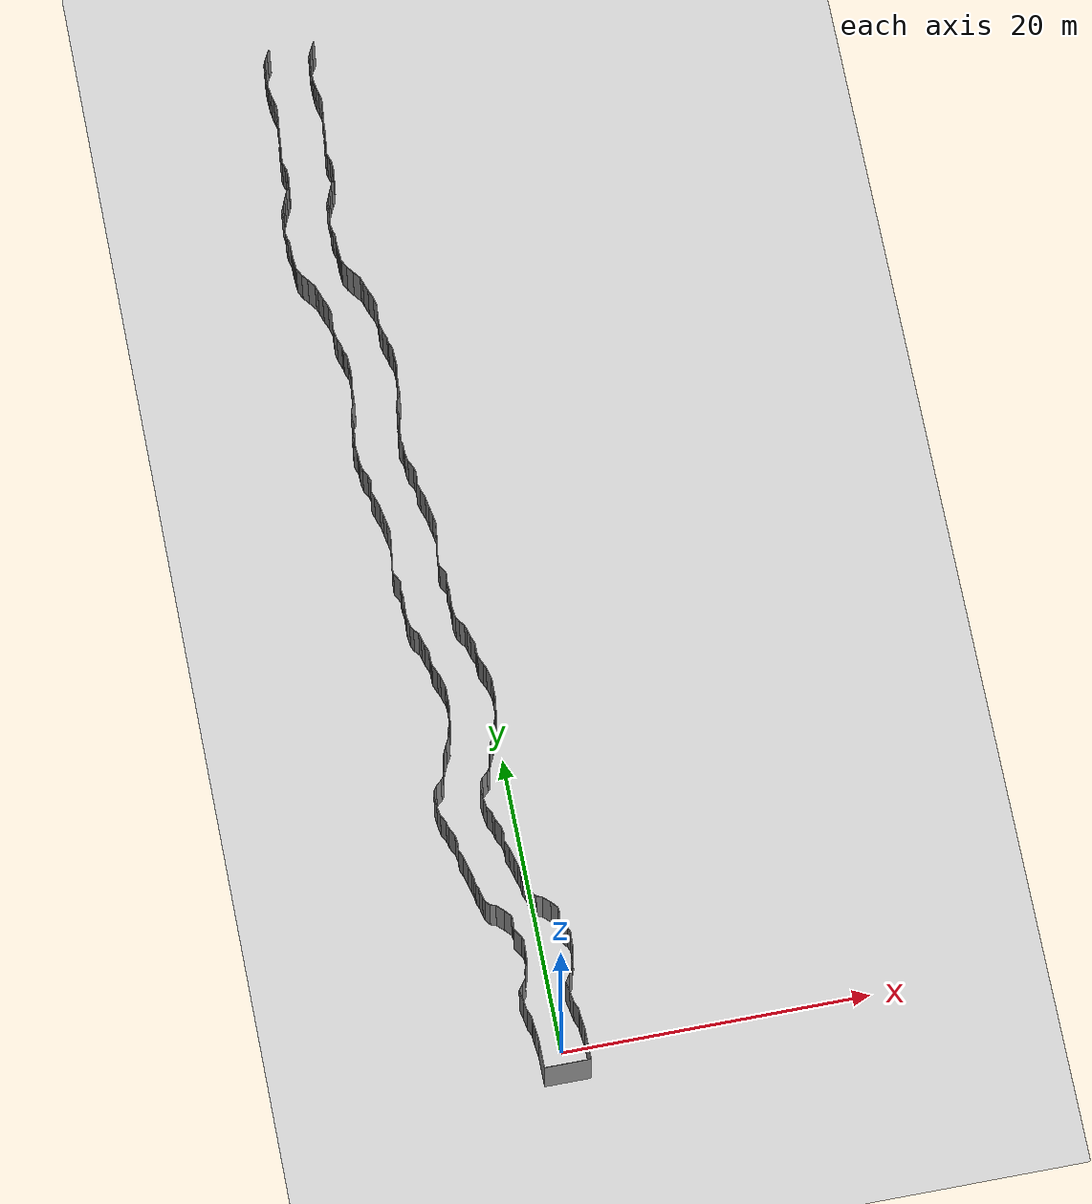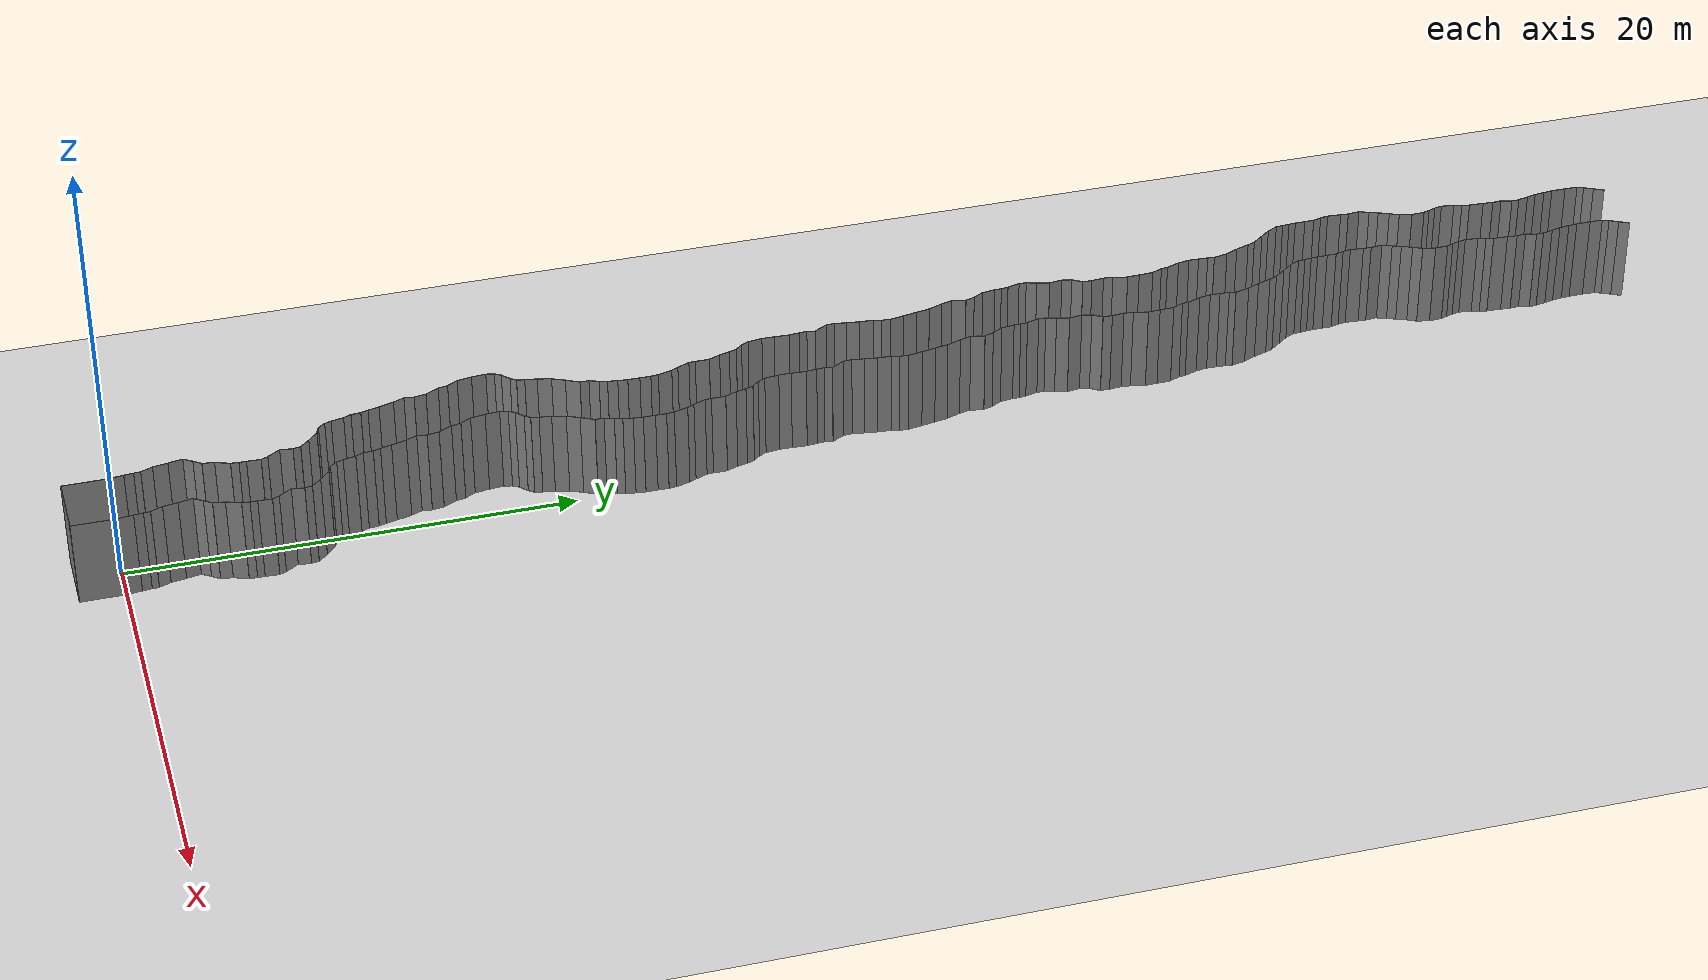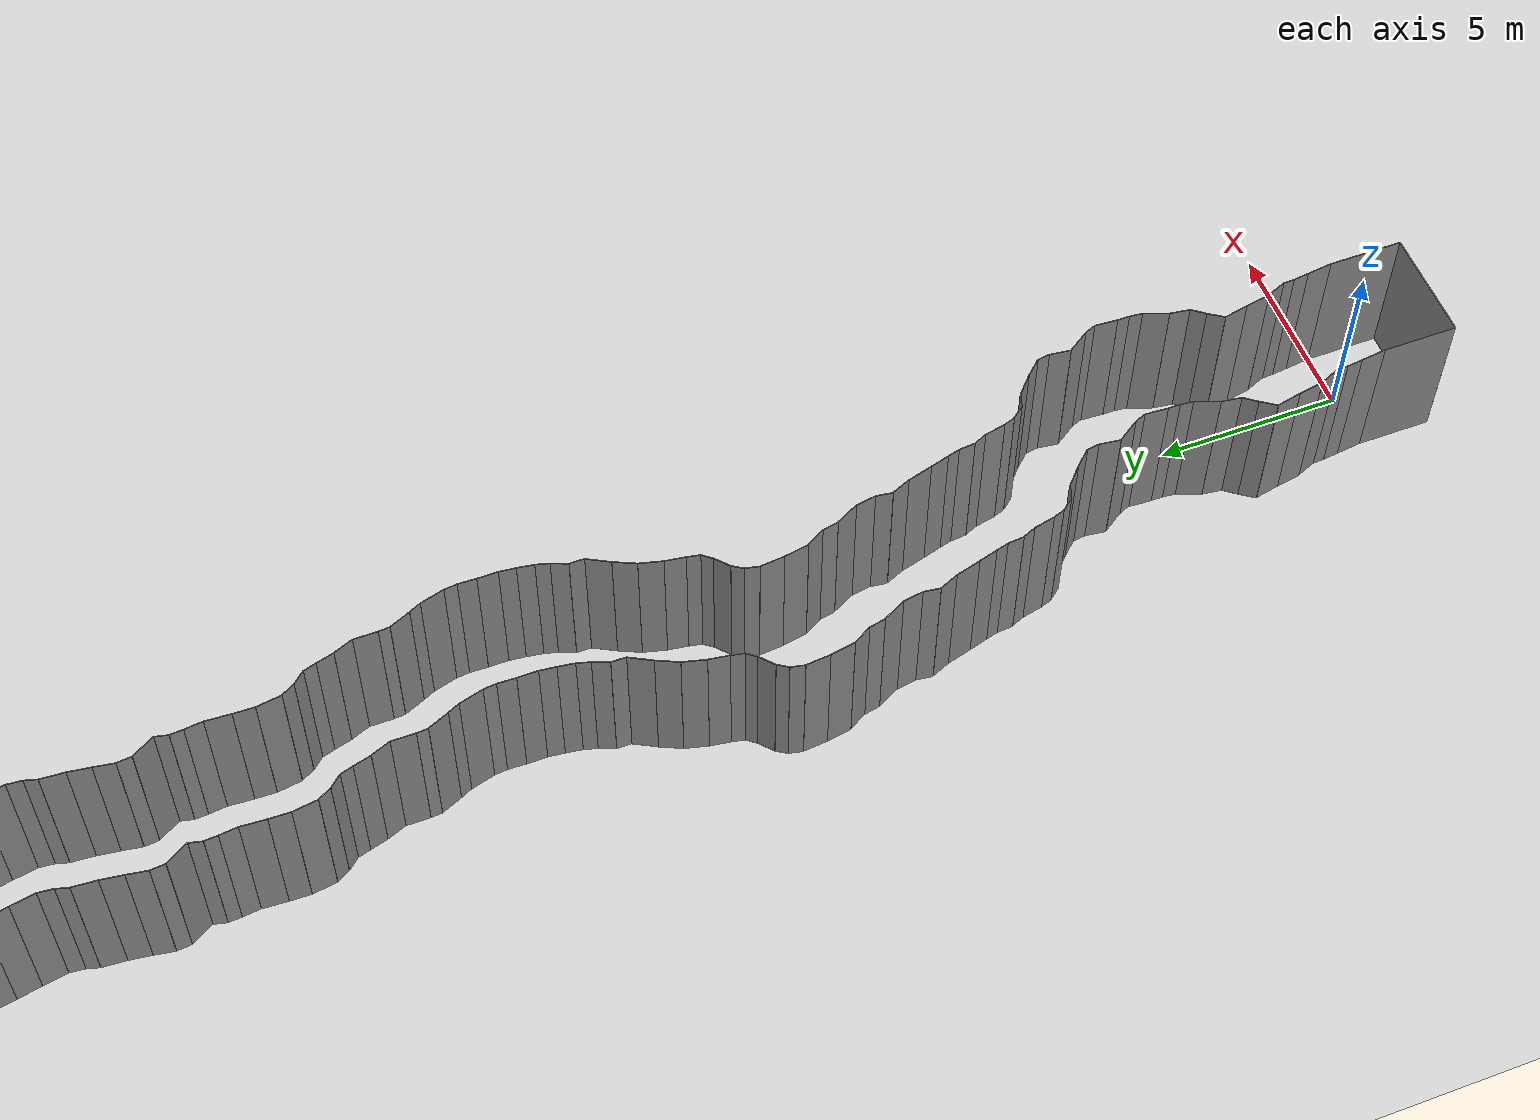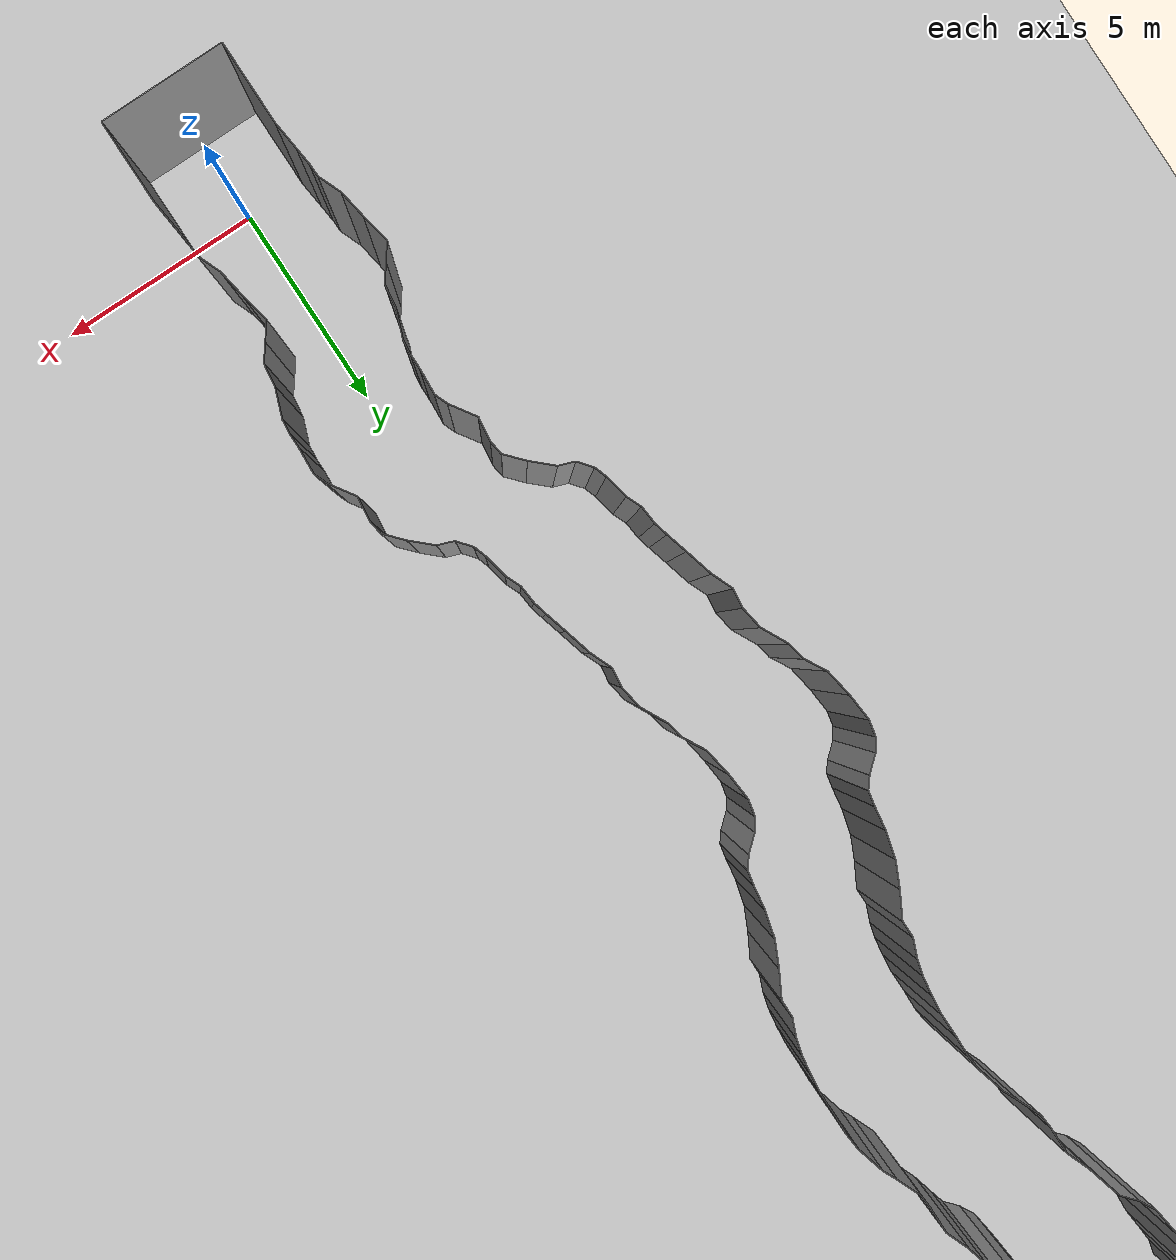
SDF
<sdf version="1.6">
 <world name="default">
  <light name="sun" type="directional">
   <pose>0 0 10 0 -0 0</pose>
   <diffuse>0.8 0.8 0.8 1</diffuse>
   <specular>0.2 0.2 0.2 1</specular>
   <attenuation>
    <range>1000</range>
    <constant>0.9</constant>
    <linear>0.01</linear>
    <quadratic>0.001</quadratic>
   </attenuation>
   <direction>-0.5 0.1 -0.9</direction>
  </light>
  <model name="ground_plane">
   <static>1</static>
   <link name="link">
    <collision name="collision">
     <geometry><plane><normal>0 0 1</normal><size>200 200</size></plane></geometry>
     <surface><friction><ode><mu>100</mu><mu2>50</mu2></ode></friction></surface>
    </collision>
    <visual name="visual">
     <cast_shadows>0</cast_shadows>
     <geometry><plane><normal>0 0 1</normal><size>200 200</size></plane></geometry>
     <material>
      <script><uri>file://media/materials/scripts/gazebo.material</uri><name>Gazebo/Grey</name></script>
     </material>
    </visual>
   </link>
   <pose>0 100 0 0 -0 0</pose>
  </model>
  <gravity>0 0 -9.8</gravity>
  <magnetic_field>6e-06 2.3e-05 -4.2e-05</magnetic_field>
  <atmosphere type="adiabatic"/>
  <physics default="0" name="default_physics" type="ode">
   <max_step_size>0.001</max_step_size>
   <real_time_factor>1</real_time_factor>
   <real_time_update_rate>1000</real_time_update_rate>
  </physics>
  <scene><ambient>0.4 0.4 0.4 1</ambient><background>0.7 0.7 0.7 1</background><shadows>1</shadows></scene>
  <spherical_coordinates>
   <surface_model>EARTH_WGS84</surface_model>
   <latitude_deg>0</latitude_deg>
   <longitude_deg>0</longitude_deg>
   <elevation>0</elevation>
   <heading_deg>0</heading_deg>
  </spherical_coordinates>
  <model name="wall_back">
   <static>1</static>
   <pose>0.0 -2 2 0.0 0 0.0</pose>
   <link name="link">
    <collision name="collision"><geometry><box><size>3 0.02 4</size></box></geometry></collision>
    <visual name="visual">
     <material>
      <script><name>Gazebo/Grey</name><uri>file://media/materials/scripts/gazebo.material</uri></script>
     </material>
     <geometry><box><size>3 0.02 4</size></box></geometry>
    </visual>
   </link>
  </model>
  <model name="wall_left">
   <static>1</static>
   <pose>1.5 -1 2 0 0 0.00</pose>
   <link name="link">
    <collision name="collision"><geometry><box><size>0.02 2 4</size></box></geometry></collision>
    <visual name="visual">
     <material>
      <script><name>Gazebo/Grey</name><uri>file://media/materials/scripts/gazebo.material</uri></script>
     </material>
     <geometry><box><size>0.02 2 4</size></box></geometry>
    </visual>
   </link>
  </model>
  <model name="wall_right">
   <static>1</static>
   <pose>-1.5 -1 2 0 0 0.00</pose>
   <link name="link">
    <collision name="collision"><geometry><box><size>0.02 2 4</size></box></geometry></collision>
    <visual name="visual">
     <material>
      <script><name>Gazebo/Grey</name><uri>file://media/materials/scripts/gazebo.material</uri></script>
     </material>
     <geometry><box><size>0.02 2 4</size></box></geometry>
    </visual>
   </link>
  </model>
  <model name="wall_0">
   <static>1</static>
   <pose>-1.539381283969348 0.34608955113164763 2 0 0 0.11330195482381757</pose>
   <link name="link">
    <collision name="collision"><geometry><box><size>0.02 0.696645858179 4</size></box></geometry></collision>
    <visual name="visual">
     <material>
      <script><name>Gazebo/Grey</name><uri>file://media/materials/scripts/gazebo.material</uri></script>
     </material>
     <geometry><box><size>0.02 0.696645858179 4</size></box></geometry>
    </visual>
   </link>
  </model>
  <model name="wall_1">
   <static>1</static>
   <pose>1.460618716030652 0.34608955113164763 2 0 0 0.11330195482381757</pose>
   <link name="link">
    <collision name="collision"><geometry><box><size>0.02 0.696645858179 4</size></box></geometry></collision>
    <visual name="visual">
     <material>
      <script><name>Gazebo/Grey</name><uri>file://media/materials/scripts/gazebo.material</uri></script>
     </material>
     <geometry><box><size>0.02 0.696645858179 4</size></box></geometry>
    </visual>
   </link>
  </model>
  <model name="wall_2">
   <static>1</static>
   <pose>-1.6018663273035938 0.903861173566263 2 0 0 0.10871336168001268</pose>
   <link name="link">
    <collision name="collision"><geometry><box><size>0.02 0.425878306599 4</size></box></geometry></collision>
    <visual name="visual">
     <material>
      <script><name>Gazebo/Grey</name><uri>file://media/materials/scripts/gazebo.material</uri></script>
     </material>
     <geometry><box><size>0.02 0.425878306599 4</size></box></geometry>
    </visual>
   </link>
  </model>
  <model name="wall_3">
   <static>1</static>
   <pose>1.3981336726964062 0.903861173566263 2 0 0 0.10871336168001268</pose>
   <link name="link">
    <collision name="collision"><geometry><box><size>0.02 0.425878306599 4</size></box></geometry></collision>
    <visual name="visual">
     <material>
      <script><name>Gazebo/Grey</name><uri>file://media/materials/scripts/gazebo.material</uri></script>
     </material>
     <geometry><box><size>0.02 0.425878306599 4</size></box></geometry>
    </visual>
   </link>
  </model>
  <model name="wall_4">
   <static>1</static>
   <pose>-1.6301238122375017 1.2685925525295065 2 0 0 0.03366090975978104</pose>
   <link name="link">
    <collision name="collision"><geometry><box><size>0.02 0.306272110794 4</size></box></geometry></collision>
    <visual name="visual">
     <material>
      <script><name>Gazebo/Grey</name><uri>file://media/materials/scripts/gazebo.material</uri></script>
     </material>
     <geometry><box><size>0.02 0.306272110794 4</size></box></geometry>
    </visual>
   </link>
  </model>
  <model name="wall_5">
   <static>1</static>
   <pose>1.3698761877624983 1.2685925525295065 2 0 0 0.03366090975978104</pose>
   <link name="link">
    <collision name="collision"><geometry><box><size>0.02 0.306272110794 4</size></box></geometry></collision>
    <visual name="visual">
     <material>
      <script><name>Gazebo/Grey</name><uri>file://media/materials/scripts/gazebo.material</uri></script>
     </material>
     <geometry><box><size>0.02 0.306272110794 4</size></box></geometry>
    </visual>
   </link>
  </model>
  <model name="wall_6">
   <static>1</static>
   <pose>-1.744771728942799 1.6880777122366888 2 0 0 0.3899178811531052</pose>
   <link name="link">
    <collision name="collision"><geometry><box><size>0.02 0.576114714787 4</size></box></geometry></collision>
    <visual name="visual">
     <material>
      <script><name>Gazebo/Grey</name><uri>file://media/materials/scripts/gazebo.material</uri></script>
     </material>
     <geometry><box><size>0.02 0.576114714787 4</size></box></geometry>
    </visual>
   </link>
  </model>
  <model name="wall_7">
   <static>1</static>
   <pose>1.255228271057201 1.6880777122366888 2 0 0 0.3899178811531052</pose>
   <link name="link">
    <collision name="collision"><geometry><box><size>0.02 0.576114714787 4</size></box></geometry></collision>
    <visual name="visual">
     <material>
      <script><name>Gazebo/Grey</name><uri>file://media/materials/scripts/gazebo.material</uri></script>
     </material>
     <geometry><box><size>0.02 0.576114714787 4</size></box></geometry>
    </visual>
   </link>
  </model>
  <model name="wall_8">
   <static>1</static>
   <pose>-1.910030564757278 2.2933393088433336 2 0 0 0.16311974463424703</pose>
   <link name="link">
    <collision name="collision"><geometry><box><size>0.02 0.686768027132 4</size></box></geometry></collision>
    <visual name="visual">
     <material>
      <script><name>Gazebo/Grey</name><uri>file://media/materials/scripts/gazebo.material</uri></script>
     </material>
     <geometry><box><size>0.02 0.686768027132 4</size></box></geometry>
    </visual>
   </link>
  </model>
  <model name="wall_9">
   <static>1</static>
   <pose>1.089969435242722 2.2933393088433336 2 0 0 0.16311974463424703</pose>
   <link name="link">
    <collision name="collision"><geometry><box><size>0.02 0.686768027132 4</size></box></geometry></collision>
    <visual name="visual">
     <material>
      <script><name>Gazebo/Grey</name><uri>file://media/materials/scripts/gazebo.material</uri></script>
     </material>
     <geometry><box><size>0.02 0.686768027132 4</size></box></geometry>
    </visual>
   </link>
  </model>
  <model name="wall_10">
   <static>1</static>
   <pose>-2.033596665253377 2.9646428908293028 2 0 0 0.20116936980153466</pose>
   <link name="link">
    <collision name="collision"><geometry><box><size>0.02 0.678641436373 4</size></box></geometry></collision>
    <visual name="visual">
     <material>
      <script><name>Gazebo/Grey</name><uri>file://media/materials/scripts/gazebo.material</uri></script>
     </material>
     <geometry><box><size>0.02 0.678641436373 4</size></box></geometry>
    </visual>
   </link>
  </model>
  <model name="wall_11">
   <static>1</static>
   <pose>0.966403334746623 2.9646428908293028 2 0 0 0.20116936980153466</pose>
   <link name="link">
    <collision name="collision"><geometry><box><size>0.02 0.678641436373 4</size></box></geometry></collision>
    <visual name="visual">
     <material>
      <script><name>Gazebo/Grey</name><uri>file://media/materials/scripts/gazebo.material</uri></script>
     </material>
     <geometry><box><size>0.02 0.678641436373 4</size></box></geometry>
    </visual>
   </link>
  </model>
  <model name="wall_12">
   <static>1</static>
   <pose>-1.9622658523186232 3.495883401475986 2 0 0 -0.6107205533705103</pose>
   <link name="link">
    <collision name="collision"><geometry><box><size>0.02 0.485239687058 4</size></box></geometry></collision>
    <visual name="visual">
     <material>
      <script><name>Gazebo/Grey</name><uri>file://media/materials/scripts/gazebo.material</uri></script>
     </material>
     <geometry><box><size>0.02 0.485239687058 4</size></box></geometry>
    </visual>
   </link>
  </model>
  <model name="wall_13">
   <static>1</static>
   <pose>1.0377341476813768 3.495883401475986 2 0 0 -0.6107205533705103</pose>
   <link name="link">
    <collision name="collision"><geometry><box><size>0.02 0.485239687058 4</size></box></geometry></collision>
    <visual name="visual">
     <material>
      <script><name>Gazebo/Grey</name><uri>file://media/materials/scripts/gazebo.material</uri></script>
     </material>
     <geometry><box><size>0.02 0.485239687058 4</size></box></geometry>
    </visual>
   </link>
  </model>
  <model name="wall_14">
   <static>1</static>
   <pose>-1.690713169516392 3.8673843807185744 2 0 0 -0.65403792310857</pose>
   <link name="link">
    <collision name="collision"><geometry><box><size>0.02 0.435309951297 4</size></box></geometry></collision>
    <visual name="visual">
     <material>
      <script><name>Gazebo/Grey</name><uri>file://media/materials/scripts/gazebo.material</uri></script>
     </material>
     <geometry><box><size>0.02 0.435309951297 4</size></box></geometry>
    </visual>
   </link>
  </model>
  <model name="wall_15">
   <static>1</static>
   <pose>1.309286830483608 3.8673843807185744 2 0 0 -0.65403792310857</pose>
   <link name="link">
    <collision name="collision"><geometry><box><size>0.02 0.435309951297 4</size></box></geometry></collision>
    <visual name="visual">
     <material>
      <script><name>Gazebo/Grey</name><uri>file://media/materials/scripts/gazebo.material</uri></script>
     </material>
     <geometry><box><size>0.02 0.435309951297 4</size></box></geometry>
    </visual>
   </link>
  </model>
  <model name="wall_16">
   <static>1</static>
   <pose>-1.5214225351436297 4.30762316468083 2 0 0 -0.13696933396929434</pose>
   <link name="link">
    <collision name="collision"><geometry><box><size>0.02 0.540058955466 4</size></box></geometry></collision>
    <visual name="visual">
     <material>
      <script><name>Gazebo/Grey</name><uri>file://media/materials/scripts/gazebo.material</uri></script>
     </material>
     <geometry><box><size>0.02 0.540058955466 4</size></box></geometry>
    </visual>
   </link>
  </model>
  <model name="wall_17">
   <static>1</static>
   <pose>1.4785774648563703 4.30762316468083 2 0 0 -0.13696933396929434</pose>
   <link name="link">
    <collision name="collision"><geometry><box><size>0.02 0.540058955466 4</size></box></geometry></collision>
    <visual name="visual">
     <material>
      <script><name>Gazebo/Grey</name><uri>file://media/materials/scripts/gazebo.material</uri></script>
     </material>
     <geometry><box><size>0.02 0.540058955466 4</size></box></geometry>
    </visual>
   </link>
  </model>
  <model name="wall_18">
   <static>1</static>
   <pose>-1.361425213174102 4.899337924793357 2 0 0 -0.36294667285411597</pose>
   <link name="link">
    <collision name="collision"><geometry><box><size>0.02 0.693614255691 4</size></box></geometry></collision>
    <visual name="visual">
     <material>
      <script><name>Gazebo/Grey</name><uri>file://media/materials/scripts/gazebo.material</uri></script>
     </material>
     <geometry><box><size>0.02 0.693614255691 4</size></box></geometry>
    </visual>
   </link>
  </model>
  <model name="wall_19">
   <static>1</static>
   <pose>1.638574786825898 4.899337924793357 2 0 0 -0.36294667285411597</pose>
   <link name="link">
    <collision name="collision"><geometry><box><size>0.02 0.693614255691 4</size></box></geometry></collision>
    <visual name="visual">
     <material>
      <script><name>Gazebo/Grey</name><uri>file://media/materials/scripts/gazebo.material</uri></script>
     </material>
     <geometry><box><size>0.02 0.693614255691 4</size></box></geometry>
    </visual>
   </link>
  </model>
  <model name="wall_20">
   <static>1</static>
   <pose>-1.2203908917650397 5.400729517939221 2 0 0 -0.10072743707660174</pose>
   <link name="link">
    <collision name="collision"><geometry><box><size>0.02 0.356159896919 4</size></box></geometry></collision>
    <visual name="visual">
     <material>
      <script><name>Gazebo/Grey</name><uri>file://media/materials/scripts/gazebo.material</uri></script>
     </material>
     <geometry><box><size>0.02 0.356159896919 4</size></box></geometry>
    </visual>
   </link>
  </model>
  <model name="wall_21">
   <static>1</static>
   <pose>1.7796091082349603 5.400729517939221 2 0 0 -0.10072743707660174</pose>
   <link name="link">
    <collision name="collision"><geometry><box><size>0.02 0.356159896919 4</size></box></geometry></collision>
    <visual name="visual">
     <material>
      <script><name>Gazebo/Grey</name><uri>file://media/materials/scripts/gazebo.material</uri></script>
     </material>
     <geometry><box><size>0.02 0.356159896919 4</size></box></geometry>
    </visual>
   </link>
  </model>
  <model name="wall_22">
   <static>1</static>
   <pose>-1.2024886098356897 5.740252224396053 2 0 0 3.0415604708249145e-05</pose>
   <link name="link">
    <collision name="collision"><geometry><box><size>0.02 0.324690791117 4</size></box></geometry></collision>
    <visual name="visual">
     <material>
      <script><name>Gazebo/Grey</name><uri>file://media/materials/scripts/gazebo.material</uri></script>
     </material>
     <geometry><box><size>0.02 0.324690791117 4</size></box></geometry>
    </visual>
   </link>
  </model>
  <model name="wall_23">
   <static>1</static>
   <pose>1.7975113901643103 5.740252224396053 2 0 0 3.0415604708249145e-05</pose>
   <link name="link">
    <collision name="collision"><geometry><box><size>0.02 0.324690791117 4</size></box></geometry></collision>
    <visual name="visual">
     <material>
      <script><name>Gazebo/Grey</name><uri>file://media/materials/scripts/gazebo.material</uri></script>
     </material>
     <geometry><box><size>0.02 0.324690791117 4</size></box></geometry>
    </visual>
   </link>
  </model>
  <model name="wall_24">
   <static>1</static>
   <pose>-1.1829643800035627 6.215769120135279 2 0 0 -0.0622786948214693</pose>
   <link name="link">
    <collision name="collision"><geometry><box><size>0.02 0.627559644854 4</size></box></geometry></collision>
    <visual name="visual">
     <material>
      <script><name>Gazebo/Grey</name><uri>file://media/materials/scripts/gazebo.material</uri></script>
     </material>
     <geometry><box><size>0.02 0.627559644854 4</size></box></geometry>
    </visual>
   </link>
  </model>
  <model name="wall_25">
   <static>1</static>
   <pose>1.8170356199964373 6.215769120135279 2 0 0 -0.0622786948214693</pose>
   <link name="link">
    <collision name="collision"><geometry><box><size>0.02 0.627559644854 4</size></box></geometry></collision>
    <visual name="visual">
     <material>
      <script><name>Gazebo/Grey</name><uri>file://media/materials/scripts/gazebo.material</uri></script>
     </material>
     <geometry><box><size>0.02 0.627559644854 4</size></box></geometry>
    </visual>
   </link>
  </model>
  <model name="wall_26">
   <static>1</static>
   <pose>-1.2245567676177287 6.681485203351496 2 0 0 0.38109240008205464</pose>
   <link name="link">
    <collision name="collision"><geometry><box><size>0.02 0.328668187145 4</size></box></geometry></collision>
    <visual name="visual">
     <material>
      <script><name>Gazebo/Grey</name><uri>file://media/materials/scripts/gazebo.material</uri></script>
     </material>
     <geometry><box><size>0.02 0.328668187145 4</size></box></geometry>
    </visual>
   </link>
  </model>
  <model name="wall_27">
   <static>1</static>
   <pose>1.7754432323822713 6.681485203351496 2 0 0 0.38109240008205464</pose>
   <link name="link">
    <collision name="collision"><geometry><box><size>0.02 0.328668187145 4</size></box></geometry></collision>
    <visual name="visual">
     <material>
      <script><name>Gazebo/Grey</name><uri>file://media/materials/scripts/gazebo.material</uri></script>
     </material>
     <geometry><box><size>0.02 0.328668187145 4</size></box></geometry>
    </visual>
   </link>
  </model>
  <model name="wall_28">
   <static>1</static>
   <pose>-1.476400186071474 7.122371808876059 2 0 0 0.5843776173376058</pose>
   <link name="link">
    <collision name="collision"><geometry><box><size>0.02 0.69142158216 4</size></box></geometry></collision>
    <visual name="visual">
     <material>
      <script><name>Gazebo/Grey</name><uri>file://media/materials/scripts/gazebo.material</uri></script>
     </material>
     <geometry><box><size>0.02 0.69142158216 4</size></box></geometry>
    </visual>
   </link>
  </model>
  <model name="wall_29">
   <static>1</static>
   <pose>1.523599813928526 7.122371808876059 2 0 0 0.5843776173376058</pose>
   <link name="link">
    <collision name="collision"><geometry><box><size>0.02 0.69142158216 4</size></box></geometry></collision>
    <visual name="visual">
     <material>
      <script><name>Gazebo/Grey</name><uri>file://media/materials/scripts/gazebo.material</uri></script>
     </material>
     <geometry><box><size>0.02 0.69142158216 4</size></box></geometry>
    </visual>
   </link>
  </model>
  <model name="wall_30">
   <static>1</static>
   <pose>-1.6308915984765664 7.696252702916271 2 0 0 -0.12621004858549317</pose>
   <link name="link">
    <collision name="collision"><geometry><box><size>0.02 0.575656469387 4</size></box></geometry></collision>
    <visual name="visual">
     <material>
      <script><name>Gazebo/Grey</name><uri>file://media/materials/scripts/gazebo.material</uri></script>
     </material>
     <geometry><box><size>0.02 0.575656469387 4</size></box></geometry>
    </visual>
   </link>
  </model>
  <model name="wall_31">
   <static>1</static>
   <pose>1.3691084015234336 7.696252702916271 2 0 0 -0.12621004858549317</pose>
   <link name="link">
    <collision name="collision"><geometry><box><size>0.02 0.575656469387 4</size></box></geometry></collision>
    <visual name="visual">
     <material>
      <script><name>Gazebo/Grey</name><uri>file://media/materials/scripts/gazebo.material</uri></script>
     </material>
     <geometry><box><size>0.02 0.575656469387 4</size></box></geometry>
    </visual>
   </link>
  </model>
  <model name="wall_32">
   <static>1</static>
   <pose>-1.6194561827558813 8.150694453887189 2 0 0 0.1457594388169777</pose>
   <link name="link">
    <collision name="collision"><geometry><box><size>0.02 0.341426281734 4</size></box></geometry></collision>
    <visual name="visual">
     <material>
      <script><name>Gazebo/Grey</name><uri>file://media/materials/scripts/gazebo.material</uri></script>
     </material>
     <geometry><box><size>0.02 0.341426281734 4</size></box></geometry>
    </visual>
   </link>
  </model>
  <model name="wall_33">
   <static>1</static>
   <pose>1.3805438172441187 8.150694453887189 2 0 0 0.1457594388169777</pose>
   <link name="link">
    <collision name="collision"><geometry><box><size>0.02 0.341426281734 4</size></box></geometry></collision>
    <visual name="visual">
     <material>
      <script><name>Gazebo/Grey</name><uri>file://media/materials/scripts/gazebo.material</uri></script>
     </material>
     <geometry><box><size>0.02 0.341426281734 4</size></box></geometry>
    </visual>
   </link>
  </model>
  <model name="wall_34">
   <static>1</static>
   <pose>-1.8318253145332912 8.526874529124926 2 0 0 0.7355394694841793</pose>
   <link name="link">
    <collision name="collision"><geometry><box><size>0.02 0.559098837912 4</size></box></geometry></collision>
    <visual name="visual">
     <material>
      <script><name>Gazebo/Grey</name><uri>file://media/materials/scripts/gazebo.material</uri></script>
     </material>
     <geometry><box><size>0.02 0.559098837912 4</size></box></geometry>
    </visual>
   </link>
  </model>
  <model name="wall_35">
   <static>1</static>
   <pose>1.1681746854667088 8.526874529124926 2 0 0 0.7355394694841793</pose>
   <link name="link">
    <collision name="collision"><geometry><box><size>0.02 0.559098837912 4</size></box></geometry></collision>
    <visual name="visual">
     <material>
      <script><name>Gazebo/Grey</name><uri>file://media/materials/scripts/gazebo.material</uri></script>
     </material>
     <geometry><box><size>0.02 0.559098837912 4</size></box></geometry>
    </visual>
   </link>
  </model>
  <model name="wall_36">
   <static>1</static>
   <pose>-2.250692934909788 8.949747068734915 2 0 0 0.8205114292339593</pose>
   <link name="link">
    <collision name="collision"><geometry><box><size>0.02 0.632386104776 4</size></box></geometry></collision>
    <visual name="visual">
     <material>
      <script><name>Gazebo/Grey</name><uri>file://media/materials/scripts/gazebo.material</uri></script>
     </material>
     <geometry><box><size>0.02 0.632386104776 4</size></box></geometry>
    </visual>
   </link>
  </model>
  <model name="wall_37">
   <static>1</static>
   <pose>0.7493070650902118 8.949747068734915 2 0 0 0.8205114292339593</pose>
   <link name="link">
    <collision name="collision"><geometry><box><size>0.02 0.632386104776 4</size></box></geometry></collision>
    <visual name="visual">
     <material>
      <script><name>Gazebo/Grey</name><uri>file://media/materials/scripts/gazebo.material</uri></script>
     </material>
     <geometry><box><size>0.02 0.632386104776 4</size></box></geometry>
    </visual>
   </link>
  </model>
  <model name="wall_38">
   <static>1</static>
   <pose>-2.6641135031653933 9.230572026008586 2 0 0 1.226875505391086</pose>
   <link name="link">
    <collision name="collision"><geometry><box><size>0.02 0.386911684201 4</size></box></geometry></collision>
    <visual name="visual">
     <material>
      <script><name>Gazebo/Grey</name><uri>file://media/materials/scripts/gazebo.material</uri></script>
     </material>
     <geometry><box><size>0.02 0.386911684201 4</size></box></geometry>
    </visual>
   </link>
  </model>
  <model name="wall_39">
   <static>1</static>
   <pose>0.3358864968346067 9.230572026008586 2 0 0 1.226875505391086</pose>
   <link name="link">
    <collision name="collision"><geometry><box><size>0.02 0.386911684201 4</size></box></geometry></collision>
    <visual name="visual">
     <material>
      <script><name>Gazebo/Grey</name><uri>file://media/materials/scripts/gazebo.material</uri></script>
     </material>
     <geometry><box><size>0.02 0.386911684201 4</size></box></geometry>
    </visual>
   </link>
  </model>
  <model name="wall_40">
   <static>1</static>
   <pose>-2.9756150246463164 9.454474165030165 2 0 0 0.684034021752631</pose>
   <link name="link">
    <collision name="collision"><geometry><box><size>0.02 0.409461723003 4</size></box></geometry></collision>
    <visual name="visual">
     <material>
      <script><name>Gazebo/Grey</name><uri>file://media/materials/scripts/gazebo.material</uri></script>
     </material>
     <geometry><box><size>0.02 0.409461723003 4</size></box></geometry>
    </visual>
   </link>
  </model>
  <model name="wall_41">
   <static>1</static>
   <pose>0.024384975353683558 9.454474165030165 2 0 0 0.684034021752631</pose>
   <link name="link">
    <collision name="collision"><geometry><box><size>0.02 0.409461723003 4</size></box></geometry></collision>
    <visual name="visual">
     <material>
      <script><name>Gazebo/Grey</name><uri>file://media/materials/scripts/gazebo.material</uri></script>
     </material>
     <geometry><box><size>0.02 0.409461723003 4</size></box></geometry>
    </visual>
   </link>
  </model>
  <model name="wall_42">
   <static>1</static>
   <pose>-3.1544555731821977 9.763482437870543 2 0 0 0.31787917403633137</pose>
   <link name="link">
    <collision name="collision"><geometry><box><size>0.02 0.31652948766 4</size></box></geometry></collision>
    <visual name="visual">
     <material>
      <script><name>Gazebo/Grey</name><uri>file://media/materials/scripts/gazebo.material</uri></script>
     </material>
     <geometry><box><size>0.02 0.31652948766 4</size></box></geometry>
    </visual>
   </link>
  </model>
  <model name="wall_43">
   <static>1</static>
   <pose>-0.15445557318219771 9.763482437870543 2 0 0 0.31787917403633137</pose>
   <link name="link">
    <collision name="collision"><geometry><box><size>0.02 0.31652948766 4</size></box></geometry></collision>
    <visual name="visual">
     <material>
      <script><name>Gazebo/Grey</name><uri>file://media/materials/scripts/gazebo.material</uri></script>
     </material>
     <geometry><box><size>0.02 0.31652948766 4</size></box></geometry>
    </visual>
   </link>
  </model>
  <model name="wall_44">
   <static>1</static>
   <pose>-3.2632362361509677 10.199207949157067 2 0 0 0.20491978559406746</pose>
   <link name="link">
    <collision name="collision"><geometry><box><size>0.02 0.582976974409 4</size></box></geometry></collision>
    <visual name="visual">
     <material>
      <script><name>Gazebo/Grey</name><uri>file://media/materials/scripts/gazebo.material</uri></script>
     </material>
     <geometry><box><size>0.02 0.582976974409 4</size></box></geometry>
    </visual>
   </link>
  </model>
  <model name="wall_45">
   <static>1</static>
   <pose>-0.2632362361509677 10.199207949157067 2 0 0 0.20491978559406746</pose>
   <link name="link">
    <collision name="collision"><geometry><box><size>0.02 0.582976974409 4</size></box></geometry></collision>
    <visual name="visual">
     <material>
      <script><name>Gazebo/Grey</name><uri>file://media/materials/scripts/gazebo.material</uri></script>
     </material>
     <geometry><box><size>0.02 0.582976974409 4</size></box></geometry>
    </visual>
   </link>
  </model>
  <model name="wall_46">
   <static>1</static>
   <pose>-3.3968194300057477 10.65912502667023 2 0 0 0.4023291541690551</pose>
   <link name="link">
    <collision name="collision"><geometry><box><size>0.02 0.379344742762 4</size></box></geometry></collision>
    <visual name="visual">
     <material>
      <script><name>Gazebo/Grey</name><uri>file://media/materials/scripts/gazebo.material</uri></script>
     </material>
     <geometry><box><size>0.02 0.379344742762 4</size></box></geometry>
    </visual>
   </link>
  </model>
  <model name="wall_47">
   <static>1</static>
   <pose>-0.3968194300057477 10.65912502667023 2 0 0 0.4023291541690551</pose>
   <link name="link">
    <collision name="collision"><geometry><box><size>0.02 0.379344742762 4</size></box></geometry></collision>
    <visual name="visual">
     <material>
      <script><name>Gazebo/Grey</name><uri>file://media/materials/scripts/gazebo.material</uri></script>
     </material>
     <geometry><box><size>0.02 0.379344742762 4</size></box></geometry>
    </visual>
   </link>
  </model>
  <model name="wall_48">
   <static>1</static>
   <pose>-3.49074988619568 11.055350759250157 2 0 0 0.08845595671554057</pose>
   <link name="link">
    <collision name="collision"><geometry><box><size>0.02 0.445137181248 4</size></box></geometry></collision>
    <visual name="visual">
     <material>
      <script><name>Gazebo/Grey</name><uri>file://media/materials/scripts/gazebo.material</uri></script>
     </material>
     <geometry><box><size>0.02 0.445137181248 4</size></box></geometry>
    </visual>
   </link>
  </model>
  <model name="wall_49">
   <static>1</static>
   <pose>-0.49074988619568005 11.055350759250157 2 0 0 0.08845595671554057</pose>
   <link name="link">
    <collision name="collision"><geometry><box><size>0.02 0.445137181248 4</size></box></geometry></collision>
    <visual name="visual">
     <material>
      <script><name>Gazebo/Grey</name><uri>file://media/materials/scripts/gazebo.material</uri></script>
     </material>
     <geometry><box><size>0.02 0.445137181248 4</size></box></geometry>
    </visual>
   </link>
  </model>
  <model name="wall_50">
   <static>1</static>
   <pose>-3.553028492758474 11.442021798303815 2 0 0 0.2527996213761783</pose>
   <link name="link">
    <collision name="collision"><geometry><box><size>0.02 0.340776483665 4</size></box></geometry></collision>
    <visual name="visual">
     <material>
      <script><name>Gazebo/Grey</name><uri>file://media/materials/scripts/gazebo.material</uri></script>
     </material>
     <geometry><box><size>0.02 0.340776483665 4</size></box></geometry>
    </visual>
   </link>
  </model>
  <model name="wall_51">
   <static>1</static>
   <pose>-0.5530284927584739 11.442021798303815 2 0 0 0.2527996213761783</pose>
   <link name="link">
    <collision name="collision"><geometry><box><size>0.02 0.340776483665 4</size></box></geometry></collision>
    <visual name="visual">
     <material>
      <script><name>Gazebo/Grey</name><uri>file://media/materials/scripts/gazebo.material</uri></script>
     </material>
     <geometry><box><size>0.02 0.340776483665 4</size></box></geometry>
    </visual>
   </link>
  </model>
  <model name="wall_52">
   <static>1</static>
   <pose>-3.665826721437401 11.862270101137563 2 0 0 0.26829578569841434</pose>
   <link name="link">
    <collision name="collision"><geometry><box><size>0.02 0.529494528106 4</size></box></geometry></collision>
    <visual name="visual">
     <material>
      <script><name>Gazebo/Grey</name><uri>file://media/materials/scripts/gazebo.material</uri></script>
     </material>
     <geometry><box><size>0.02 0.529494528106 4</size></box></geometry>
    </visual>
   </link>
  </model>
  <model name="wall_53">
   <static>1</static>
   <pose>-0.665826721437401 11.862270101137563 2 0 0 0.26829578569841434</pose>
   <link name="link">
    <collision name="collision"><geometry><box><size>0.02 0.529494528106 4</size></box></geometry></collision>
    <visual name="visual">
     <material>
      <script><name>Gazebo/Grey</name><uri>file://media/materials/scripts/gazebo.material</uri></script>
     </material>
     <geometry><box><size>0.02 0.529494528106 4</size></box></geometry>
    </visual>
   </link>
  </model>
  <model name="wall_54">
   <static>1</static>
   <pose>-3.8258063287665083 12.454246231493508 2 0 0 0.26063385075908957</pose>
   <link name="link">
    <collision name="collision"><geometry><box><size>0.02 0.696938722544 4</size></box></geometry></collision>
    <visual name="visual">
     <material>
      <script><name>Gazebo/Grey</name><uri>file://media/materials/scripts/gazebo.material</uri></script>
     </material>
     <geometry><box><size>0.02 0.696938722544 4</size></box></geometry>
    </visual>
   </link>
  </model>
  <model name="wall_55">
   <static>1</static>
   <pose>-0.8258063287665083 12.454246231493508 2 0 0 0.26063385075908957</pose>
   <link name="link">
    <collision name="collision"><geometry><box><size>0.02 0.696938722544 4</size></box></geometry></collision>
    <visual name="visual">
     <material>
      <script><name>Gazebo/Grey</name><uri>file://media/materials/scripts/gazebo.material</uri></script>
     </material>
     <geometry><box><size>0.02 0.696938722544 4</size></box></geometry>
    </visual>
   </link>
  </model>
  <model name="wall_56">
   <static>1</static>
   <pose>-4.019517550081671 13.040960848418301 2 0 0 0.39390645956759857</pose>
   <link name="link">
    <collision name="collision"><geometry><box><size>0.02 0.541497978423 4</size></box></geometry></collision>
    <visual name="visual">
     <material>
      <script><name>Gazebo/Grey</name><uri>file://media/materials/scripts/gazebo.material</uri></script>
     </material>
     <geometry><box><size>0.02 0.541497978423 4</size></box></geometry>
    </visual>
   </link>
  </model>
  <model name="wall_57">
   <static>1</static>
   <pose>-1.0195175500816713 13.040960848418301 2 0 0 0.39390645956759857</pose>
   <link name="link">
    <collision name="collision"><geometry><box><size>0.02 0.541497978423 4</size></box></geometry></collision>
    <visual name="visual">
     <material>
      <script><name>Gazebo/Grey</name><uri>file://media/materials/scripts/gazebo.material</uri></script>
     </material>
     <geometry><box><size>0.02 0.541497978423 4</size></box></geometry>
    </visual>
   </link>
  </model>
  <model name="wall_58">
   <static>1</static>
   <pose>-4.094032278653399 13.514378021306259 2 0 0 -0.13084160440009943</pose>
   <link name="link">
    <collision name="collision"><geometry><box><size>0.02 0.450658032537 4</size></box></geometry></collision>
    <visual name="visual">
     <material>
      <script><name>Gazebo/Grey</name><uri>file://media/materials/scripts/gazebo.material</uri></script>
     </material>
     <geometry><box><size>0.02 0.450658032537 4</size></box></geometry>
    </visual>
   </link>
  </model>
  <model name="wall_59">
   <static>1</static>
   <pose>-1.0940322786533994 13.514378021306259 2 0 0 -0.13084160440009943</pose>
   <link name="link">
    <collision name="collision"><geometry><box><size>0.02 0.450658032537 4</size></box></geometry></collision>
    <visual name="visual">
     <material>
      <script><name>Gazebo/Grey</name><uri>file://media/materials/scripts/gazebo.material</uri></script>
     </material>
     <geometry><box><size>0.02 0.450658032537 4</size></box></geometry>
    </visual>
   </link>
  </model>
  <model name="wall_60">
   <static>1</static>
   <pose>-4.107554099085519 14.007343003974347 2 0 0 0.1578965325324809</pose>
   <link name="link">
    <collision name="collision"><geometry><box><size>0.02 0.545915021408 4</size></box></geometry></collision>
    <visual name="visual">
     <material>
      <script><name>Gazebo/Grey</name><uri>file://media/materials/scripts/gazebo.material</uri></script>
     </material>
     <geometry><box><size>0.02 0.545915021408 4</size></box></geometry>
    </visual>
   </link>
  </model>
  <model name="wall_61">
   <static>1</static>
   <pose>-1.1075540990855188 14.007343003974347 2 0 0 0.1578965325324809</pose>
   <link name="link">
    <collision name="collision"><geometry><box><size>0.02 0.545915021408 4</size></box></geometry></collision>
    <visual name="visual">
     <material>
      <script><name>Gazebo/Grey</name><uri>file://media/materials/scripts/gazebo.material</uri></script>
     </material>
     <geometry><box><size>0.02 0.545915021408 4</size></box></geometry>
    </visual>
   </link>
  </model>
  <model name="wall_62">
   <static>1</static>
   <pose>-4.302991172112162 14.577854216884841 2 0 0 0.4690617475597031</pose>
   <link name="link">
    <collision name="collision"><geometry><box><size>0.02 0.674779500003 4</size></box></geometry></collision>
    <visual name="visual">
     <material>
      <script><name>Gazebo/Grey</name><uri>file://media/materials/scripts/gazebo.material</uri></script>
     </material>
     <geometry><box><size>0.02 0.674779500003 4</size></box></geometry>
    </visual>
   </link>
  </model>
  <model name="wall_63">
   <static>1</static>
   <pose>-1.3029911721121623 14.577854216884841 2 0 0 0.4690617475597031</pose>
   <link name="link">
    <collision name="collision"><geometry><box><size>0.02 0.674779500003 4</size></box></geometry></collision>
    <visual name="visual">
     <material>
      <script><name>Gazebo/Grey</name><uri>file://media/materials/scripts/gazebo.material</uri></script>
     </material>
     <geometry><box><size>0.02 0.674779500003 4</size></box></geometry>
    </visual>
   </link>
  </model>
  <model name="wall_64">
   <static>1</static>
   <pose>-4.499990120058984 15.097223299326723 2 0 0 0.20090645469880206</pose>
   <link name="link">
    <collision name="collision"><geometry><box><size>0.02 0.445806611424 4</size></box></geometry></collision>
    <visual name="visual">
     <material>
      <script><name>Gazebo/Grey</name><uri>file://media/materials/scripts/gazebo.material</uri></script>
     </material>
     <geometry><box><size>0.02 0.445806611424 4</size></box></geometry>
    </visual>
   </link>
  </model>
  <model name="wall_65">
   <static>1</static>
   <pose>-1.4999901200589836 15.097223299326723 2 0 0 0.20090645469880206</pose>
   <link name="link">
    <collision name="collision"><geometry><box><size>0.02 0.445806611424 4</size></box></geometry></collision>
    <visual name="visual">
     <material>
      <script><name>Gazebo/Grey</name><uri>file://media/materials/scripts/gazebo.material</uri></script>
     </material>
     <geometry><box><size>0.02 0.445806611424 4</size></box></geometry>
    </visual>
   </link>
  </model>
  <model name="wall_66">
   <static>1</static>
   <pose>-4.679886187158877 15.55493133657857 2 0 0 0.5149711075867297</pose>
   <link name="link">
    <collision name="collision"><geometry><box><size>0.02 0.549893776646 4</size></box></geometry></collision>
    <visual name="visual">
     <material>
      <script><name>Gazebo/Grey</name><uri>file://media/materials/scripts/gazebo.material</uri></script>
     </material>
     <geometry><box><size>0.02 0.549893776646 4</size></box></geometry>
    </visual>
   </link>
  </model>
  <model name="wall_67">
   <static>1</static>
   <pose>-1.6798861871588766 15.55493133657857 2 0 0 0.5149711075867297</pose>
   <link name="link">
    <collision name="collision"><geometry><box><size>0.02 0.549893776646 4</size></box></geometry></collision>
    <visual name="visual">
     <material>
      <script><name>Gazebo/Grey</name><uri>file://media/materials/scripts/gazebo.material</uri></script>
     </material>
     <geometry><box><size>0.02 0.549893776646 4</size></box></geometry>
    </visual>
   </link>
  </model>
  <model name="wall_68">
   <static>1</static>
   <pose>-4.870622647442466 16.128074211602293 2 0 0 0.1642159429641677</pose>
   <link name="link">
    <collision name="collision"><geometry><box><size>0.02 0.676814672358 4</size></box></geometry></collision>
    <visual name="visual">
     <material>
      <script><name>Gazebo/Grey</name><uri>file://media/materials/scripts/gazebo.material</uri></script>
     </material>
     <geometry><box><size>0.02 0.676814672358 4</size></box></geometry>
    </visual>
   </link>
  </model>
  <model name="wall_69">
   <static>1</static>
   <pose>-1.8706226474424659 16.128074211602293 2 0 0 0.1642159429641677</pose>
   <link name="link">
    <collision name="collision"><geometry><box><size>0.02 0.676814672358 4</size></box></geometry></collision>
    <visual name="visual">
     <material>
      <script><name>Gazebo/Grey</name><uri>file://media/materials/scripts/gazebo.material</uri></script>
     </material>
     <geometry><box><size>0.02 0.676814672358 4</size></box></geometry>
    </visual>
   </link>
  </model>
  <model name="wall_70">
   <static>1</static>
   <pose>-4.953774103943977 16.789921392292083 2 0 0 0.08464374832966867</pose>
   <link name="link">
    <collision name="collision"><geometry><box><size>0.02 0.65834194709 4</size></box></geometry></collision>
    <visual name="visual">
     <material>
      <script><name>Gazebo/Grey</name><uri>file://media/materials/scripts/gazebo.material</uri></script>
     </material>
     <geometry><box><size>0.02 0.65834194709 4</size></box></geometry>
    </visual>
   </link>
  </model>
  <model name="wall_71">
   <static>1</static>
   <pose>-1.953774103943977 16.789921392292083 2 0 0 0.08464374832966867</pose>
   <link name="link">
    <collision name="collision"><geometry><box><size>0.02 0.65834194709 4</size></box></geometry></collision>
    <visual name="visual">
     <material>
      <script><name>Gazebo/Grey</name><uri>file://media/materials/scripts/gazebo.material</uri></script>
     </material>
     <geometry><box><size>0.02 0.65834194709 4</size></box></geometry>
    </visual>
   </link>
  </model>
  <model name="wall_72">
   <static>1</static>
   <pose>-4.940597926242914 17.303504752749035 2 0 0 -0.21745052618434096</pose>
   <link name="link">
    <collision name="collision"><geometry><box><size>0.02 0.380133633448 4</size></box></geometry></collision>
    <visual name="visual">
     <material>
      <script><name>Gazebo/Grey</name><uri>file://media/materials/scripts/gazebo.material</uri></script>
     </material>
     <geometry><box><size>0.02 0.380133633448 4</size></box></geometry>
    </visual>
   </link>
  </model>
  <model name="wall_73">
   <static>1</static>
   <pose>-1.9405979262429138 17.303504752749035 2 0 0 -0.21745052618434096</pose>
   <link name="link">
    <collision name="collision"><geometry><box><size>0.02 0.380133633448 4</size></box></geometry></collision>
    <visual name="visual">
     <material>
      <script><name>Gazebo/Grey</name><uri>file://media/materials/scripts/gazebo.material</uri></script>
     </material>
     <geometry><box><size>0.02 0.380133633448 4</size></box></geometry>
    </visual>
   </link>
  </model>
  <model name="wall_74">
   <static>1</static>
   <pose>-4.8090508543106 17.62739112944181 2 0 0 -0.5796712429326525</pose>
   <link name="link">
    <collision name="collision"><geometry><box><size>0.02 0.330596319204 4</size></box></geometry></collision>
    <visual name="visual">
     <material>
      <script><name>Gazebo/Grey</name><uri>file://media/materials/scripts/gazebo.material</uri></script>
     </material>
     <geometry><box><size>0.02 0.330596319204 4</size></box></geometry>
    </visual>
   </link>
  </model>
  <model name="wall_75">
   <static>1</static>
   <pose>-1.8090508543106 17.62739112944181 2 0 0 -0.5796712429326525</pose>
   <link name="link">
    <collision name="collision"><geometry><box><size>0.02 0.330596319204 4</size></box></geometry></collision>
    <visual name="visual">
     <material>
      <script><name>Gazebo/Grey</name><uri>file://media/materials/scripts/gazebo.material</uri></script>
     </material>
     <geometry><box><size>0.02 0.330596319204 4</size></box></geometry>
    </visual>
   </link>
  </model>
  <model name="wall_76">
   <static>1</static>
   <pose>-4.537655444849806 17.924619260666404 2 0 0 -0.8498227007358027</pose>
   <link name="link">
    <collision name="collision"><geometry><box><size>0.02 0.48152912436 4</size></box></geometry></collision>
    <visual name="visual">
     <material>
      <script><name>Gazebo/Grey</name><uri>file://media/materials/scripts/gazebo.material</uri></script>
     </material>
     <geometry><box><size>0.02 0.48152912436 4</size></box></geometry>
    </visual>
   </link>
  </model>
  <model name="wall_77">
   <static>1</static>
   <pose>-1.5376554448498059 17.924619260666404 2 0 0 -0.8498227007358027</pose>
   <link name="link">
    <collision name="collision"><geometry><box><size>0.02 0.48152912436 4</size></box></geometry></collision>
    <visual name="visual">
     <material>
      <script><name>Gazebo/Grey</name><uri>file://media/materials/scripts/gazebo.material</uri></script>
     </material>
     <geometry><box><size>0.02 0.48152912436 4</size></box></geometry>
    </visual>
   </link>
  </model>
  <model name="wall_78">
   <static>1</static>
   <pose>-4.259291106532988 18.207845466338775 2 0 0 -0.6652304515447082</pose>
   <link name="link">
    <collision name="collision"><geometry><box><size>0.02 0.315957304203 4</size></box></geometry></collision>
    <visual name="visual">
     <material>
      <script><name>Gazebo/Grey</name><uri>file://media/materials/scripts/gazebo.material</uri></script>
     </material>
     <geometry><box><size>0.02 0.315957304203 4</size></box></geometry>
    </visual>
   </link>
  </model>
  <model name="wall_79">
   <static>1</static>
   <pose>-1.259291106532988 18.207845466338775 2 0 0 -0.6652304515447082</pose>
   <link name="link">
    <collision name="collision"><geometry><box><size>0.02 0.315957304203 4</size></box></geometry></collision>
    <visual name="visual">
     <material>
      <script><name>Gazebo/Grey</name><uri>file://media/materials/scripts/gazebo.material</uri></script>
     </material>
     <geometry><box><size>0.02 0.315957304203 4</size></box></geometry>
    </visual>
   </link>
  </model>
  <model name="wall_80">
   <static>1</static>
   <pose>-4.125946687361028 18.506785651148704 2 0 0 -0.20236920765686695</pose>
   <link name="link">
    <collision name="collision"><geometry><box><size>0.02 0.356569667727 4</size></box></geometry></collision>
    <visual name="visual">
     <material>
      <script><name>Gazebo/Grey</name><uri>file://media/materials/scripts/gazebo.material</uri></script>
     </material>
     <geometry><box><size>0.02 0.356569667727 4</size></box></geometry>
    </visual>
   </link>
  </model>
  <model name="wall_81">
   <static>1</static>
   <pose>-1.1259466873610284 18.506785651148704 2 0 0 -0.20236920765686695</pose>
   <link name="link">
    <collision name="collision"><geometry><box><size>0.02 0.356569667727 4</size></box></geometry></collision>
    <visual name="visual">
     <material>
      <script><name>Gazebo/Grey</name><uri>file://media/materials/scripts/gazebo.material</uri></script>
     </material>
     <geometry><box><size>0.02 0.356569667727 4</size></box></geometry>
    </visual>
   </link>
  </model>
  <model name="wall_82">
   <static>1</static>
   <pose>-4.04897732088072 18.95326960595 2 0 0 -0.15018545184946558</pose>
   <link name="link">
    <collision name="collision"><geometry><box><size>0.02 0.549864341503 4</size></box></geometry></collision>
    <visual name="visual">
     <material>
      <script><name>Gazebo/Grey</name><uri>file://media/materials/scripts/gazebo.material</uri></script>
     </material>
     <geometry><box><size>0.02 0.549864341503 4</size></box></geometry>
    </visual>
   </link>
  </model>
  <model name="wall_83">
   <static>1</static>
   <pose>-1.04897732088072 18.95326960595 2 0 0 -0.15018545184946558</pose>
   <link name="link">
    <collision name="collision"><geometry><box><size>0.02 0.549864341503 4</size></box></geometry></collision>
    <visual name="visual">
     <material>
      <script><name>Gazebo/Grey</name><uri>file://media/materials/scripts/gazebo.material</uri></script>
     </material>
     <geometry><box><size>0.02 0.549864341503 4</size></box></geometry>
    </visual>
   </link>
  </model>
  <model name="wall_84">
   <static>1</static>
   <pose>-3.9269397103972743 19.532441080749784 2 0 0 -0.2573981066082973</pose>
   <link name="link">
    <collision name="collision"><geometry><box><size>0.02 0.63560796138 4</size></box></geometry></collision>
    <visual name="visual">
     <material>
      <script><name>Gazebo/Grey</name><uri>file://media/materials/scripts/gazebo.material</uri></script>
     </material>
     <geometry><box><size>0.02 0.63560796138 4</size></box></geometry>
    </visual>
   </link>
  </model>
  <model name="wall_85">
   <static>1</static>
   <pose>-0.9269397103972743 19.532441080749784 2 0 0 -0.2573981066082973</pose>
   <link name="link">
    <collision name="collision"><geometry><box><size>0.02 0.63560796138 4</size></box></geometry></collision>
    <visual name="visual">
     <material>
      <script><name>Gazebo/Grey</name><uri>file://media/materials/scripts/gazebo.material</uri></script>
     </material>
     <geometry><box><size>0.02 0.63560796138 4</size></box></geometry>
    </visual>
   </link>
  </model>
  <model name="wall_86">
   <static>1</static>
   <pose>-3.7129688123274525 20.12234572424565 2 0 0 -0.44011688636229307</pose>
   <link name="link">
    <collision name="collision"><geometry><box><size>0.02 0.624671027455 4</size></box></geometry></collision>
    <visual name="visual">
     <material>
      <script><name>Gazebo/Grey</name><uri>file://media/materials/scripts/gazebo.material</uri></script>
     </material>
     <geometry><box><size>0.02 0.624671027455 4</size></box></geometry>
    </visual>
   </link>
  </model>
  <model name="wall_87">
   <static>1</static>
   <pose>-0.7129688123274525 20.12234572424565 2 0 0 -0.44011688636229307</pose>
   <link name="link">
    <collision name="collision"><geometry><box><size>0.02 0.624671027455 4</size></box></geometry></collision>
    <visual name="visual">
     <material>
      <script><name>Gazebo/Grey</name><uri>file://media/materials/scripts/gazebo.material</uri></script>
     </material>
     <geometry><box><size>0.02 0.624671027455 4</size></box></geometry>
    </visual>
   </link>
  </model>
  <model name="wall_88">
   <static>1</static>
   <pose>-3.420305541735166 20.697100015111737 2 0 0 -0.49993014691435805</pose>
   <link name="link">
    <collision name="collision"><geometry><box><size>0.02 0.665857849032 4</size></box></geometry></collision>
    <visual name="visual">
     <material>
      <script><name>Gazebo/Grey</name><uri>file://media/materials/scripts/gazebo.material</uri></script>
     </material>
     <geometry><box><size>0.02 0.665857849032 4</size></box></geometry>
    </visual>
   </link>
  </model>
  <model name="wall_89">
   <static>1</static>
   <pose>-0.420305541735166 20.697100015111737 2 0 0 -0.49993014691435805</pose>
   <link name="link">
    <collision name="collision"><geometry><box><size>0.02 0.665857849032 4</size></box></geometry></collision>
    <visual name="visual">
     <material>
      <script><name>Gazebo/Grey</name><uri>file://media/materials/scripts/gazebo.material</uri></script>
     </material>
     <geometry><box><size>0.02 0.665857849032 4</size></box></geometry>
    </visual>
   </link>
  </model>
  <model name="wall_90">
   <static>1</static>
   <pose>-3.260210312977813 21.188671209015144 2 0 0 -0.002512737673673849</pose>
   <link name="link">
    <collision name="collision"><geometry><box><size>0.02 0.398776111981 4</size></box></geometry></collision>
    <visual name="visual">
     <material>
      <script><name>Gazebo/Grey</name><uri>file://media/materials/scripts/gazebo.material</uri></script>
     </material>
     <geometry><box><size>0.02 0.398776111981 4</size></box></geometry>
    </visual>
   </link>
  </model>
  <model name="wall_91">
   <static>1</static>
   <pose>-0.26021031297781283 21.188671209015144 2 0 0 -0.002512737673673849</pose>
   <link name="link">
    <collision name="collision"><geometry><box><size>0.02 0.398776111981 4</size></box></geometry></collision>
    <visual name="visual">
     <material>
      <script><name>Gazebo/Grey</name><uri>file://media/materials/scripts/gazebo.material</uri></script>
     </material>
     <geometry><box><size>0.02 0.398776111981 4</size></box></geometry>
    </visual>
   </link>
  </model>
  <model name="wall_92">
   <static>1</static>
   <pose>-3.1736822961100652 21.59933822921421 2 0 0 -0.38667328824647956</pose>
   <link name="link">
    <collision name="collision"><geometry><box><size>0.02 0.456244288598 4</size></box></geometry></collision>
    <visual name="visual">
     <material>
      <script><name>Gazebo/Grey</name><uri>file://media/materials/scripts/gazebo.material</uri></script>
     </material>
     <geometry><box><size>0.02 0.456244288598 4</size></box></geometry>
    </visual>
   </link>
  </model>
  <model name="wall_93">
   <static>1</static>
   <pose>-0.17368229611006525 21.59933822921421 2 0 0 -0.38667328824647956</pose>
   <link name="link">
    <collision name="collision"><geometry><box><size>0.02 0.456244288598 4</size></box></geometry></collision>
    <visual name="visual">
     <material>
      <script><name>Gazebo/Grey</name><uri>file://media/materials/scripts/gazebo.material</uri></script>
     </material>
     <geometry><box><size>0.02 0.456244288598 4</size></box></geometry>
    </visual>
   </link>
  </model>
  <model name="wall_94">
   <static>1</static>
   <pose>-3.0388098046685807 21.98840284275133 2 0 0 -0.26812880307506903</pose>
   <link name="link">
    <collision name="collision"><geometry><box><size>0.02 0.368745953699 4</size></box></geometry></collision>
    <visual name="visual">
     <material>
      <script><name>Gazebo/Grey</name><uri>file://media/materials/scripts/gazebo.material</uri></script>
     </material>
     <geometry><box><size>0.02 0.368745953699 4</size></box></geometry>
    </visual>
   </link>
  </model>
  <model name="wall_95">
   <static>1</static>
   <pose>-0.03880980466858075 21.98840284275133 2 0 0 -0.26812880307506903</pose>
   <link name="link">
    <collision name="collision"><geometry><box><size>0.02 0.368745953699 4</size></box></geometry></collision>
    <visual name="visual">
     <material>
      <script><name>Gazebo/Grey</name><uri>file://media/materials/scripts/gazebo.material</uri></script>
     </material>
     <geometry><box><size>0.02 0.368745953699 4</size></box></geometry>
    </visual>
   </link>
  </model>
  <model name="wall_96">
   <static>1</static>
   <pose>-2.9558455337147396 22.38895846555877 2 0 0 -0.15197564346339834</pose>
   <link name="link">
    <collision name="collision"><geometry><box><size>0.02 0.450736433667 4</size></box></geometry></collision>
    <visual name="visual">
     <material>
      <script><name>Gazebo/Grey</name><uri>file://media/materials/scripts/gazebo.material</uri></script>
     </material>
     <geometry><box><size>0.02 0.450736433667 4</size></box></geometry>
    </visual>
   </link>
  </model>
  <model name="wall_97">
   <static>1</static>
   <pose>0.04415446628526043 22.38895846555877 2 0 0 -0.15197564346339834</pose>
   <link name="link">
    <collision name="collision"><geometry><box><size>0.02 0.450736433667 4</size></box></geometry></collision>
    <visual name="visual">
     <material>
      <script><name>Gazebo/Grey</name><uri>file://media/materials/scripts/gazebo.material</uri></script>
     </material>
     <geometry><box><size>0.02 0.450736433667 4</size></box></geometry>
    </visual>
   </link>
  </model>
  <model name="wall_98">
   <static>1</static>
   <pose>-2.8978779430872943 22.832247988667863 2 0 0 -0.10772985492441707</pose>
   <link name="link">
    <collision name="collision"><geometry><box><size>0.02 0.443609556206 4</size></box></geometry></collision>
    <visual name="visual">
     <material>
      <script><name>Gazebo/Grey</name><uri>file://media/materials/scripts/gazebo.material</uri></script>
     </material>
     <geometry><box><size>0.02 0.443609556206 4</size></box></geometry>
    </visual>
   </link>
  </model>
  <model name="wall_99">
   <static>1</static>
   <pose>0.1021220569127057 22.832247988667863 2 0 0 -0.10772985492441707</pose>
   <link name="link">
    <collision name="collision"><geometry><box><size>0.02 0.443609556206 4</size></box></geometry></collision>
    <visual name="visual">
     <material>
      <script><name>Gazebo/Grey</name><uri>file://media/materials/scripts/gazebo.material</uri></script>
     </material>
     <geometry><box><size>0.02 0.443609556206 4</size></box></geometry>
    </visual>
   </link>
  </model>
  <model name="wall_100">
   <static>1</static>
   <pose>-2.8746633524548444 23.32493147671447 2 0 0 0.002330251232430163</pose>
   <link name="link">
    <collision name="collision"><geometry><box><size>0.02 0.544330613614 4</size></box></geometry></collision>
    <visual name="visual">
     <material>
      <script><name>Gazebo/Grey</name><uri>file://media/materials/scripts/gazebo.material</uri></script>
     </material>
     <geometry><box><size>0.02 0.544330613614 4</size></box></geometry>
    </visual>
   </link>
  </model>
  <model name="wall_101">
   <static>1</static>
   <pose>0.1253366475451556 23.32493147671447 2 0 0 0.002330251232430163</pose>
   <link name="link">
    <collision name="collision"><geometry><box><size>0.02 0.544330613614 4</size></box></geometry></collision>
    <visual name="visual">
     <material>
      <script><name>Gazebo/Grey</name><uri>file://media/materials/scripts/gazebo.material</uri></script>
     </material>
     <geometry><box><size>0.02 0.544330613614 4</size></box></geometry>
    </visual>
   </link>
  </model>
  <model name="wall_102">
   <static>1</static>
   <pose>-2.867491743651207 23.843409387798804 2 0 0 -0.03168001427152603</pose>
   <link name="link">
    <collision name="collision"><geometry><box><size>0.02 0.49287399566 4</size></box></geometry></collision>
    <visual name="visual">
     <material>
      <script><name>Gazebo/Grey</name><uri>file://media/materials/scripts/gazebo.material</uri></script>
     </material>
     <geometry><box><size>0.02 0.49287399566 4</size></box></geometry>
    </visual>
   </link>
  </model>
  <model name="wall_103">
   <static>1</static>
   <pose>0.13250825634879293 23.843409387798804 2 0 0 -0.03168001427152603</pose>
   <link name="link">
    <collision name="collision"><geometry><box><size>0.02 0.49287399566 4</size></box></geometry></collision>
    <visual name="visual">
     <material>
      <script><name>Gazebo/Grey</name><uri>file://media/materials/scripts/gazebo.material</uri></script>
     </material>
     <geometry><box><size>0.02 0.49287399566 4</size></box></geometry>
    </visual>
   </link>
  </model>
  <model name="wall_104">
   <static>1</static>
   <pose>-2.8774471590715085 24.262781407084322 2 0 0 0.10227321723112542</pose>
   <link name="link">
    <collision name="collision"><geometry><box><size>0.02 0.347935436021 4</size></box></geometry></collision>
    <visual name="visual">
     <material>
      <script><name>Gazebo/Grey</name><uri>file://media/materials/scripts/gazebo.material</uri></script>
     </material>
     <geometry><box><size>0.02 0.347935436021 4</size></box></geometry>
    </visual>
   </link>
  </model>
  <model name="wall_105">
   <static>1</static>
   <pose>0.1225528409284915 24.262781407084322 2 0 0 0.10227321723112542</pose>
   <link name="link">
    <collision name="collision"><geometry><box><size>0.02 0.347935436021 4</size></box></geometry></collision>
    <visual name="visual">
     <material>
      <script><name>Gazebo/Grey</name><uri>file://media/materials/scripts/gazebo.material</uri></script>
     </material>
     <geometry><box><size>0.02 0.347935436021 4</size></box></geometry>
    </visual>
   </link>
  </model>
  <model name="wall_106">
   <static>1</static>
   <pose>-2.982223274780329 24.758961858371904 2 0 0 0.2630540434338525</pose>
   <link name="link">
    <collision name="collision"><geometry><box><size>0.02 0.669266077739 4</size></box></geometry></collision>
    <visual name="visual">
     <material>
      <script><name>Gazebo/Grey</name><uri>file://media/materials/scripts/gazebo.material</uri></script>
     </material>
     <geometry><box><size>0.02 0.669266077739 4</size></box></geometry>
    </visual>
   </link>
  </model>
  <model name="wall_107">
   <static>1</static>
   <pose>0.017776725219670997 24.758961858371904 2 0 0 0.2630540434338525</pose>
   <link name="link">
    <collision name="collision"><geometry><box><size>0.02 0.669266077739 4</size></box></geometry></collision>
    <visual name="visual">
     <material>
      <script><name>Gazebo/Grey</name><uri>file://media/materials/scripts/gazebo.material</uri></script>
     </material>
     <geometry><box><size>0.02 0.669266077739 4</size></box></geometry>
    </visual>
   </link>
  </model>
  <model name="wall_108">
   <static>1</static>
   <pose>-3.142261080793354 25.237744187463523 2 0 0 0.4386369593004954</pose>
   <link name="link">
    <collision name="collision"><geometry><box><size>0.02 0.343875302821 4</size></box></geometry></collision>
    <visual name="visual">
     <material>
      <script><name>Gazebo/Grey</name><uri>file://media/materials/scripts/gazebo.material</uri></script>
     </material>
     <geometry><box><size>0.02 0.343875302821 4</size></box></geometry>
    </visual>
   </link>
  </model>
  <model name="wall_109">
   <static>1</static>
   <pose>-0.1422610807933542 25.237744187463523 2 0 0 0.4386369593004954</pose>
   <link name="link">
    <collision name="collision"><geometry><box><size>0.02 0.343875302821 4</size></box></geometry></collision>
    <visual name="visual">
     <material>
      <script><name>Gazebo/Grey</name><uri>file://media/materials/scripts/gazebo.material</uri></script>
     </material>
     <geometry><box><size>0.02 0.343875302821 4</size></box></geometry>
    </visual>
   </link>
  </model>
  <model name="wall_110">
   <static>1</static>
   <pose>-3.3334440761913187 25.673499980013172 2 0 0 0.3992052793292468</pose>
   <link name="link">
    <collision name="collision"><geometry><box><size>0.02 0.607997185438 4</size></box></geometry></collision>
    <visual name="visual">
     <material>
      <script><name>Gazebo/Grey</name><uri>file://media/materials/scripts/gazebo.material</uri></script>
     </material>
     <geometry><box><size>0.02 0.607997185438 4</size></box></geometry>
    </visual>
   </link>
  </model>
  <model name="wall_111">
   <static>1</static>
   <pose>-0.33344407619131866 25.673499980013172 2 0 0 0.3992052793292468</pose>
   <link name="link">
    <collision name="collision"><geometry><box><size>0.02 0.607997185438 4</size></box></geometry></collision>
    <visual name="visual">
     <material>
      <script><name>Gazebo/Grey</name><uri>file://media/materials/scripts/gazebo.material</uri></script>
     </material>
     <geometry><box><size>0.02 0.607997185438 4</size></box></geometry>
    </visual>
   </link>
  </model>
  <model name="wall_112">
   <static>1</static>
   <pose>-3.462596429926655 26.103327900006146 2 0 0 0.07328127676391422</pose>
   <link name="link">
    <collision name="collision"><geometry><box><size>0.02 0.300271252053 4</size></box></geometry></collision>
    <visual name="visual">
     <material>
      <script><name>Gazebo/Grey</name><uri>file://media/materials/scripts/gazebo.material</uri></script>
     </material>
     <geometry><box><size>0.02 0.300271252053 4</size></box></geometry>
    </visual>
   </link>
  </model>
  <model name="wall_113">
   <static>1</static>
   <pose>-0.4625964299266552 26.103327900006146 2 0 0 0.07328127676391422</pose>
   <link name="link">
    <collision name="collision"><geometry><box><size>0.02 0.300271252053 4</size></box></geometry></collision>
    <visual name="visual">
     <material>
      <script><name>Gazebo/Grey</name><uri>file://media/materials/scripts/gazebo.material</uri></script>
     </material>
     <geometry><box><size>0.02 0.300271252053 4</size></box></geometry>
    </visual>
   </link>
  </model>
  <model name="wall_114">
   <static>1</static>
   <pose>-3.470584370145869 26.57180741230222 2 0 0 -0.00942521260801243</pose>
   <link name="link">
    <collision name="collision"><geometry><box><size>0.02 0.637521978763 4</size></box></geometry></collision>
    <visual name="visual">
     <material>
      <script><name>Gazebo/Grey</name><uri>file://media/materials/scripts/gazebo.material</uri></script>
     </material>
     <geometry><box><size>0.02 0.637521978763 4</size></box></geometry>
    </visual>
   </link>
  </model>
  <model name="wall_115">
   <static>1</static>
   <pose>-0.4705843701458692 26.57180741230222 2 0 0 -0.00942521260801243</pose>
   <link name="link">
    <collision name="collision"><geometry><box><size>0.02 0.637521978763 4</size></box></geometry></collision>
    <visual name="visual">
     <material>
      <script><name>Gazebo/Grey</name><uri>file://media/materials/scripts/gazebo.material</uri></script>
     </material>
     <geometry><box><size>0.02 0.637521978763 4</size></box></geometry>
    </visual>
   </link>
  </model>
  <model name="wall_116">
   <static>1</static>
   <pose>-3.5698808683943604 27.15019600162541 2 0 0 0.3753299240601073</pose>
   <link name="link">
    <collision name="collision"><geometry><box><size>0.02 0.558137278208 4</size></box></geometry></collision>
    <visual name="visual">
     <material>
      <script><name>Gazebo/Grey</name><uri>file://media/materials/scripts/gazebo.material</uri></script>
     </material>
     <geometry><box><size>0.02 0.558137278208 4</size></box></geometry>
    </visual>
   </link>
  </model>
  <model name="wall_117">
   <static>1</static>
   <pose>-0.5698808683943604 27.15019600162541 2 0 0 0.3753299240601073</pose>
   <link name="link">
    <collision name="collision"><geometry><box><size>0.02 0.558137278208 4</size></box></geometry></collision>
    <visual name="visual">
     <material>
      <script><name>Gazebo/Grey</name><uri>file://media/materials/scripts/gazebo.material</uri></script>
     </material>
     <geometry><box><size>0.02 0.558137278208 4</size></box></geometry>
    </visual>
   </link>
  </model>
  <model name="wall_118">
   <static>1</static>
   <pose>-3.735543475753043 27.647565002333305 2 0 0 0.26047605708628974</pose>
   <link name="link">
    <collision name="collision"><geometry><box><size>0.02 0.492052659113 4</size></box></geometry></collision>
    <visual name="visual">
     <material>
      <script><name>Gazebo/Grey</name><uri>file://media/materials/scripts/gazebo.material</uri></script>
     </material>
     <geometry><box><size>0.02 0.492052659113 4</size></box></geometry>
    </visual>
   </link>
  </model>
  <model name="wall_119">
   <static>1</static>
   <pose>-0.735543475753043 27.647565002333305 2 0 0 0.26047605708628974</pose>
   <link name="link">
    <collision name="collision"><geometry><box><size>0.02 0.492052659113 4</size></box></geometry></collision>
    <visual name="visual">
     <material>
      <script><name>Gazebo/Grey</name><uri>file://media/materials/scripts/gazebo.material</uri></script>
     </material>
     <geometry><box><size>0.02 0.492052659113 4</size></box></geometry>
    </visual>
   </link>
  </model>
  <model name="wall_120">
   <static>1</static>
   <pose>-3.8477910476879753 28.05604571693762 2 0 0 0.2788361554356456</pose>
   <link name="link">
    <collision name="collision"><geometry><box><size>0.02 0.355227085392 4</size></box></geometry></collision>
    <visual name="visual">
     <material>
      <script><name>Gazebo/Grey</name><uri>file://media/materials/scripts/gazebo.material</uri></script>
     </material>
     <geometry><box><size>0.02 0.355227085392 4</size></box></geometry>
    </visual>
   </link>
  </model>
  <model name="wall_121">
   <static>1</static>
   <pose>-0.8477910476879753 28.05604571693762 2 0 0 0.2788361554356456</pose>
   <link name="link">
    <collision name="collision"><geometry><box><size>0.02 0.355227085392 4</size></box></geometry></collision>
    <visual name="visual">
     <material>
      <script><name>Gazebo/Grey</name><uri>file://media/materials/scripts/gazebo.material</uri></script>
     </material>
     <geometry><box><size>0.02 0.355227085392 4</size></box></geometry>
    </visual>
   </link>
  </model>
  <model name="wall_122">
   <static>1</static>
   <pose>-4.0341465663588405 28.380787574687954 2 0 0 0.7287827438543323</pose>
   <link name="link">
    <collision name="collision"><geometry><box><size>0.02 0.412845463112 4</size></box></geometry></collision>
    <visual name="visual">
     <material>
      <script><name>Gazebo/Grey</name><uri>file://media/materials/scripts/gazebo.material</uri></script>
     </material>
     <geometry><box><size>0.02 0.412845463112 4</size></box></geometry>
    </visual>
   </link>
  </model>
  <model name="wall_123">
   <static>1</static>
   <pose>-1.0341465663588405 28.380787574687954 2 0 0 0.7287827438543323</pose>
   <link name="link">
    <collision name="collision"><geometry><box><size>0.02 0.412845463112 4</size></box></geometry></collision>
    <visual name="visual">
     <material>
      <script><name>Gazebo/Grey</name><uri>file://media/materials/scripts/gazebo.material</uri></script>
     </material>
     <geometry><box><size>0.02 0.412845463112 4</size></box></geometry>
    </visual>
   </link>
  </model>
  <model name="wall_124">
   <static>1</static>
   <pose>-4.2661328927459445 28.708228568697308 2 0 0 0.49892941237759486</pose>
   <link name="link">
    <collision name="collision"><geometry><box><size>0.02 0.395065554686 4</size></box></geometry></collision>
    <visual name="visual">
     <material>
      <script><name>Gazebo/Grey</name><uri>file://media/materials/scripts/gazebo.material</uri></script>
     </material>
     <geometry><box><size>0.02 0.395065554686 4</size></box></geometry>
    </visual>
   </link>
  </model>
  <model name="wall_125">
   <static>1</static>
   <pose>-1.2661328927459445 28.708228568697308 2 0 0 0.49892941237759486</pose>
   <link name="link">
    <collision name="collision"><geometry><box><size>0.02 0.395065554686 4</size></box></geometry></collision>
    <visual name="visual">
     <material>
      <script><name>Gazebo/Grey</name><uri>file://media/materials/scripts/gazebo.material</uri></script>
     </material>
     <geometry><box><size>0.02 0.395065554686 4</size></box></geometry>
    </visual>
   </link>
  </model>
  <model name="wall_126">
   <static>1</static>
   <pose>-4.406033235374218 29.2137627871852 2 0 0 0.1358229529202847</pose>
   <link name="link">
    <collision name="collision"><geometry><box><size>0.02 0.670336865526 4</size></box></geometry></collision>
    <visual name="visual">
     <material>
      <script><name>Gazebo/Grey</name><uri>file://media/materials/scripts/gazebo.material</uri></script>
     </material>
     <geometry><box><size>0.02 0.670336865526 4</size></box></geometry>
    </visual>
   </link>
  </model>
  <model name="wall_127">
   <static>1</static>
   <pose>-1.4060332353742178 29.2137627871852 2 0 0 0.1358229529202847</pose>
   <link name="link">
    <collision name="collision"><geometry><box><size>0.02 0.670336865526 4</size></box></geometry></collision>
    <visual name="visual">
     <material>
      <script><name>Gazebo/Grey</name><uri>file://media/materials/scripts/gazebo.material</uri></script>
     </material>
     <geometry><box><size>0.02 0.670336865526 4</size></box></geometry>
    </visual>
   </link>
  </model>
  <model name="wall_128">
   <static>1</static>
   <pose>-4.442783425128623 29.827902618154553 2 0 0 -0.03059950498302147</pose>
   <link name="link">
    <collision name="collision"><geometry><box><size>0.02 0.564380644528 4</size></box></geometry></collision>
    <visual name="visual">
     <material>
      <script><name>Gazebo/Grey</name><uri>file://media/materials/scripts/gazebo.material</uri></script>
     </material>
     <geometry><box><size>0.02 0.564380644528 4</size></box></geometry>
    </visual>
   </link>
  </model>
  <model name="wall_129">
   <static>1</static>
   <pose>-1.4427834251286233 29.827902618154553 2 0 0 -0.03059950498302147</pose>
   <link name="link">
    <collision name="collision"><geometry><box><size>0.02 0.564380644528 4</size></box></geometry></collision>
    <visual name="visual">
     <material>
      <script><name>Gazebo/Grey</name><uri>file://media/materials/scripts/gazebo.material</uri></script>
     </material>
     <geometry><box><size>0.02 0.564380644528 4</size></box></geometry>
    </visual>
   </link>
  </model>
  <model name="wall_130">
   <static>1</static>
   <pose>-4.413630511386044 30.448330453876512 2 0 0 -0.06056772995165061</pose>
   <link name="link">
    <collision name="collision"><geometry><box><size>0.02 0.677982421639 4</size></box></geometry></collision>
    <visual name="visual">
     <material>
      <script><name>Gazebo/Grey</name><uri>file://media/materials/scripts/gazebo.material</uri></script>
     </material>
     <geometry><box><size>0.02 0.677982421639 4</size></box></geometry>
    </visual>
   </link>
  </model>
  <model name="wall_131">
   <static>1</static>
   <pose>-1.4136305113860441 30.448330453876512 2 0 0 -0.06056772995165061</pose>
   <link name="link">
    <collision name="collision"><geometry><box><size>0.02 0.677982421639 4</size></box></geometry></collision>
    <visual name="visual">
     <material>
      <script><name>Gazebo/Grey</name><uri>file://media/materials/scripts/gazebo.material</uri></script>
     </material>
     <geometry><box><size>0.02 0.677982421639 4</size></box></geometry>
    </visual>
   </link>
  </model>
  <model name="wall_132">
   <static>1</static>
   <pose>-4.417452268027261 31.03049929908118 2 0 0 0.09951112150589234</pose>
   <link name="link">
    <collision name="collision"><geometry><box><size>0.02 0.490022675243 4</size></box></geometry></collision>
    <visual name="visual">
     <material>
      <script><name>Gazebo/Grey</name><uri>file://media/materials/scripts/gazebo.material</uri></script>
     </material>
     <geometry><box><size>0.02 0.490022675243 4</size></box></geometry>
    </visual>
   </link>
  </model>
  <model name="wall_133">
   <static>1</static>
   <pose>-1.4174522680272608 31.03049929908118 2 0 0 0.09951112150589234</pose>
   <link name="link">
    <collision name="collision"><geometry><box><size>0.02 0.490022675243 4</size></box></geometry></collision>
    <visual name="visual">
     <material>
      <script><name>Gazebo/Grey</name><uri>file://media/materials/scripts/gazebo.material</uri></script>
     </material>
     <geometry><box><size>0.02 0.490022675243 4</size></box></geometry>
    </visual>
   </link>
  </model>
  <model name="wall_134">
   <static>1</static>
   <pose>-4.452397759446966 31.450199342860486 2 0 0 0.06021313183023827</pose>
   <link name="link">
    <collision name="collision"><geometry><box><size>0.02 0.352440341211 4</size></box></geometry></collision>
    <visual name="visual">
     <material>
      <script><name>Gazebo/Grey</name><uri>file://media/materials/scripts/gazebo.material</uri></script>
     </material>
     <geometry><box><size>0.02 0.352440341211 4</size></box></geometry>
    </visual>
   </link>
  </model>
  <model name="wall_135">
   <static>1</static>
   <pose>-1.4523977594469661 31.450199342860486 2 0 0 0.06021313183023827</pose>
   <link name="link">
    <collision name="collision"><geometry><box><size>0.02 0.352440341211 4</size></box></geometry></collision>
    <visual name="visual">
     <material>
      <script><name>Gazebo/Grey</name><uri>file://media/materials/scripts/gazebo.material</uri></script>
     </material>
     <geometry><box><size>0.02 0.352440341211 4</size></box></geometry>
    </visual>
   </link>
  </model>
  <model name="wall_136">
   <static>1</static>
   <pose>-4.420408804714107 31.802904095510023 2 0 0 -0.2364024375527528</pose>
   <link name="link">
    <collision name="collision"><geometry><box><size>0.02 0.363724198991 4</size></box></geometry></collision>
    <visual name="visual">
     <material>
      <script><name>Gazebo/Grey</name><uri>file://media/materials/scripts/gazebo.material</uri></script>
     </material>
     <geometry><box><size>0.02 0.363724198991 4</size></box></geometry>
    </visual>
   </link>
  </model>
  <model name="wall_137">
   <static>1</static>
   <pose>-1.420408804714107 31.802904095510023 2 0 0 -0.2364024375527528</pose>
   <link name="link">
    <collision name="collision"><geometry><box><size>0.02 0.363724198991 4</size></box></geometry></collision>
    <visual name="visual">
     <material>
      <script><name>Gazebo/Grey</name><uri>file://media/materials/scripts/gazebo.material</uri></script>
     </material>
     <geometry><box><size>0.02 0.363724198991 4</size></box></geometry>
    </visual>
   </link>
  </model>
  <model name="wall_138">
   <static>1</static>
   <pose>-4.549807812755879 32.27759709525107 2 0 0 0.523613859895887</pose>
   <link name="link">
    <collision name="collision"><geometry><box><size>0.02 0.687951308251 4</size></box></geometry></collision>
    <visual name="visual">
     <material>
      <script><name>Gazebo/Grey</name><uri>file://media/materials/scripts/gazebo.material</uri></script>
     </material>
     <geometry><box><size>0.02 0.687951308251 4</size></box></geometry>
    </visual>
   </link>
  </model>
  <model name="wall_139">
   <static>1</static>
   <pose>-1.549807812755879 32.27759709525107 2 0 0 0.523613859895887</pose>
   <link name="link">
    <collision name="collision"><geometry><box><size>0.02 0.687951308251 4</size></box></geometry></collision>
    <visual name="visual">
     <material>
      <script><name>Gazebo/Grey</name><uri>file://media/materials/scripts/gazebo.material</uri></script>
     </material>
     <geometry><box><size>0.02 0.687951308251 4</size></box></geometry>
    </visual>
   </link>
  </model>
  <model name="wall_140">
   <static>1</static>
   <pose>-4.7385519818969115 32.77202981258373 2 0 0 0.08502670608644575</pose>
   <link name="link">
    <collision name="collision"><geometry><box><size>0.02 0.394512527101 4</size></box></geometry></collision>
    <visual name="visual">
     <material>
      <script><name>Gazebo/Grey</name><uri>file://media/materials/scripts/gazebo.material</uri></script>
     </material>
     <geometry><box><size>0.02 0.394512527101 4</size></box></geometry>
    </visual>
   </link>
  </model>
  <model name="wall_141">
   <static>1</static>
   <pose>-1.7385519818969115 32.77202981258373 2 0 0 0.08502670608644575</pose>
   <link name="link">
    <collision name="collision"><geometry><box><size>0.02 0.394512527101 4</size></box></geometry></collision>
    <visual name="visual">
     <material>
      <script><name>Gazebo/Grey</name><uri>file://media/materials/scripts/gazebo.material</uri></script>
     </material>
     <geometry><box><size>0.02 0.394512527101 4</size></box></geometry>
    </visual>
   </link>
  </model>
  <model name="wall_142">
   <static>1</static>
   <pose>-4.709135393654167 33.24128518625957 2 0 0 -0.16770383435737424</pose>
   <link name="link">
    <collision name="collision"><geometry><box><size>0.02 0.553184255069 4</size></box></geometry></collision>
    <visual name="visual">
     <material>
      <script><name>Gazebo/Grey</name><uri>file://media/materials/scripts/gazebo.material</uri></script>
     </material>
     <geometry><box><size>0.02 0.553184255069 4</size></box></geometry>
    </visual>
   </link>
  </model>
  <model name="wall_143">
   <static>1</static>
   <pose>-1.709135393654167 33.24128518625957 2 0 0 -0.16770383435737424</pose>
   <link name="link">
    <collision name="collision"><geometry><box><size>0.02 0.553184255069 4</size></box></geometry></collision>
    <visual name="visual">
     <material>
      <script><name>Gazebo/Grey</name><uri>file://media/materials/scripts/gazebo.material</uri></script>
     </material>
     <geometry><box><size>0.02 0.553184255069 4</size></box></geometry>
    </visual>
   </link>
  </model>
  <model name="wall_144">
   <static>1</static>
   <pose>-4.62195610250301 33.8095677220869 2 0 0 -0.1378710988783205</pose>
   <link name="link">
    <collision name="collision"><geometry><box><size>0.02 0.596804823239 4</size></box></geometry></collision>
    <visual name="visual">
     <material>
      <script><name>Gazebo/Grey</name><uri>file://media/materials/scripts/gazebo.material</uri></script>
     </material>
     <geometry><box><size>0.02 0.596804823239 4</size></box></geometry>
    </visual>
   </link>
  </model>
  <model name="wall_145">
   <static>1</static>
   <pose>-1.6219561025030096 33.8095677220869 2 0 0 -0.1378710988783205</pose>
   <link name="link">
    <collision name="collision"><geometry><box><size>0.02 0.596804823239 4</size></box></geometry></collision>
    <visual name="visual">
     <material>
      <script><name>Gazebo/Grey</name><uri>file://media/materials/scripts/gazebo.material</uri></script>
     </material>
     <geometry><box><size>0.02 0.596804823239 4</size></box></geometry>
    </visual>
   </link>
  </model>
  <model name="wall_146">
   <static>1</static>
   <pose>-4.5583322153672245 34.42650926945965 2 0 0 -0.07024853618579469</pose>
   <link name="link">
    <collision name="collision"><geometry><box><size>0.02 0.644330642633 4</size></box></geometry></collision>
    <visual name="visual">
     <material>
      <script><name>Gazebo/Grey</name><uri>file://media/materials/scripts/gazebo.material</uri></script>
     </material>
     <geometry><box><size>0.02 0.644330642633 4</size></box></geometry>
    </visual>
   </link>
  </model>
  <model name="wall_147">
   <static>1</static>
   <pose>-1.5583322153672245 34.42650926945965 2 0 0 -0.07024853618579469</pose>
   <link name="link">
    <collision name="collision"><geometry><box><size>0.02 0.644330642633 4</size></box></geometry></collision>
    <visual name="visual">
     <material>
      <script><name>Gazebo/Grey</name><uri>file://media/materials/scripts/gazebo.material</uri></script>
     </material>
     <geometry><box><size>0.02 0.644330642633 4</size></box></geometry>
    </visual>
   </link>
  </model>
  <model name="wall_148">
   <static>1</static>
   <pose>-4.487543233944392 34.91481203085667 2 0 0 -0.2809620271610667</pose>
   <link name="link">
    <collision name="collision"><geometry><box><size>0.02 0.347489428314 4</size></box></geometry></collision>
    <visual name="visual">
     <material>
      <script><name>Gazebo/Grey</name><uri>file://media/materials/scripts/gazebo.material</uri></script>
     </material>
     <geometry><box><size>0.02 0.347489428314 4</size></box></geometry>
    </visual>
   </link>
  </model>
  <model name="wall_149">
   <static>1</static>
   <pose>-1.4875432339443924 34.91481203085667 2 0 0 -0.2809620271610667</pose>
   <link name="link">
    <collision name="collision"><geometry><box><size>0.02 0.347489428314 4</size></box></geometry></collision>
    <visual name="visual">
     <material>
      <script><name>Gazebo/Grey</name><uri>file://media/materials/scripts/gazebo.material</uri></script>
     </material>
     <geometry><box><size>0.02 0.347489428314 4</size></box></geometry>
    </visual>
   </link>
  </model>
  <model name="wall_150">
   <static>1</static>
   <pose>-4.420657843224259 35.28480763675786 2 0 0 -0.09187649113899805</pose>
   <link name="link">
    <collision name="collision"><geometry><box><size>0.02 0.4078473137 4</size></box></geometry></collision>
    <visual name="visual">
     <material>
      <script><name>Gazebo/Grey</name><uri>file://media/materials/scripts/gazebo.material</uri></script>
     </material>
     <geometry><box><size>0.02 0.4078473137 4</size></box></geometry>
    </visual>
   </link>
  </model>
  <model name="wall_151">
   <static>1</static>
   <pose>-1.4206578432242587 35.28480763675786 2 0 0 -0.09187649113899805</pose>
   <link name="link">
    <collision name="collision"><geometry><box><size>0.02 0.4078473137 4</size></box></geometry></collision>
    <visual name="visual">
     <material>
      <script><name>Gazebo/Grey</name><uri>file://media/materials/scripts/gazebo.material</uri></script>
     </material>
     <geometry><box><size>0.02 0.4078473137 4</size></box></geometry>
    </visual>
   </link>
  </model>
  <model name="wall_152">
   <static>1</static>
   <pose>-4.45735182879271 35.81775944817107 2 0 0 0.16639322718188904</pose>
   <link name="link">
    <collision name="collision"><geometry><box><size>0.02 0.669016561162 4</size></box></geometry></collision>
    <visual name="visual">
     <material>
      <script><name>Gazebo/Grey</name><uri>file://media/materials/scripts/gazebo.material</uri></script>
     </material>
     <geometry><box><size>0.02 0.669016561162 4</size></box></geometry>
    </visual>
   </link>
  </model>
  <model name="wall_153">
   <static>1</static>
   <pose>-1.45735182879271 35.81775944817107 2 0 0 0.16639322718188904</pose>
   <link name="link">
    <collision name="collision"><geometry><box><size>0.02 0.669016561162 4</size></box></geometry></collision>
    <visual name="visual">
     <material>
      <script><name>Gazebo/Grey</name><uri>file://media/materials/scripts/gazebo.material</uri></script>
     </material>
     <geometry><box><size>0.02 0.669016561162 4</size></box></geometry>
    </visual>
   </link>
  </model>
  <model name="wall_154">
   <static>1</static>
   <pose>-4.575995451840966 36.46799275689906 2 0 0 0.19490656850193167</pose>
   <link name="link">
    <collision name="collision"><geometry><box><size>0.02 0.653055238869 4</size></box></geometry></collision>
    <visual name="visual">
     <material>
      <script><name>Gazebo/Grey</name><uri>file://media/materials/scripts/gazebo.material</uri></script>
     </material>
     <geometry><box><size>0.02 0.653055238869 4</size></box></geometry>
    </visual>
   </link>
  </model>
  <model name="wall_155">
   <static>1</static>
   <pose>-1.5759954518409662 36.46799275689906 2 0 0 0.19490656850193167</pose>
   <link name="link">
    <collision name="collision"><geometry><box><size>0.02 0.653055238869 4</size></box></geometry></collision>
    <visual name="visual">
     <material>
      <script><name>Gazebo/Grey</name><uri>file://media/materials/scripts/gazebo.material</uri></script>
     </material>
     <geometry><box><size>0.02 0.653055238869 4</size></box></geometry>
    </visual>
   </link>
  </model>
  <model name="wall_156">
   <static>1</static>
   <pose>-4.6920308699164615 37.092213756995 2 0 0 0.17202226703404905</pose>
   <link name="link">
    <collision name="collision"><geometry><box><size>0.02 0.61685627618 4</size></box></geometry></collision>
    <visual name="visual">
     <material>
      <script><name>Gazebo/Grey</name><uri>file://media/materials/scripts/gazebo.material</uri></script>
     </material>
     <geometry><box><size>0.02 0.61685627618 4</size></box></geometry>
    </visual>
   </link>
  </model>
  <model name="wall_157">
   <static>1</static>
   <pose>-1.6920308699164615 37.092213756995 2 0 0 0.17202226703404905</pose>
   <link name="link">
    <collision name="collision"><geometry><box><size>0.02 0.61685627618 4</size></box></geometry></collision>
    <visual name="visual">
     <material>
      <script><name>Gazebo/Grey</name><uri>file://media/materials/scripts/gazebo.material</uri></script>
     </material>
     <geometry><box><size>0.02 0.61685627618 4</size></box></geometry>
    </visual>
   </link>
  </model>
  <model name="wall_158">
   <static>1</static>
   <pose>-4.85910208446116 37.72054103686596 2 0 0 0.33864497295321705</pose>
   <link name="link">
    <collision name="collision"><geometry><box><size>0.02 0.687975815708 4</size></box></geometry></collision>
    <visual name="visual">
     <material>
      <script><name>Gazebo/Grey</name><uri>file://media/materials/scripts/gazebo.material</uri></script>
     </material>
     <geometry><box><size>0.02 0.687975815708 4</size></box></geometry>
    </visual>
   </link>
  </model>
  <model name="wall_159">
   <static>1</static>
   <pose>-1.8591020844611599 37.72054103686596 2 0 0 0.33864497295321705</pose>
   <link name="link">
    <collision name="collision"><geometry><box><size>0.02 0.687975815708 4</size></box></geometry></collision>
    <visual name="visual">
     <material>
      <script><name>Gazebo/Grey</name><uri>file://media/materials/scripts/gazebo.material</uri></script>
     </material>
     <geometry><box><size>0.02 0.687975815708 4</size></box></geometry>
    </visual>
   </link>
  </model>
  <model name="wall_160">
   <static>1</static>
   <pose>-5.0479114627293376 38.305604805208546 2 0 0 0.27855752877716256</pose>
   <link name="link">
    <collision name="collision"><geometry><box><size>0.02 0.542121972802 4</size></box></geometry></collision>
    <visual name="visual">
     <material>
      <script><name>Gazebo/Grey</name><uri>file://media/materials/scripts/gazebo.material</uri></script>
     </material>
     <geometry><box><size>0.02 0.542121972802 4</size></box></geometry>
    </visual>
   </link>
  </model>
  <model name="wall_161">
   <static>1</static>
   <pose>-2.0479114627293376 38.305604805208546 2 0 0 0.27855752877716256</pose>
   <link name="link">
    <collision name="collision"><geometry><box><size>0.02 0.542121972802 4</size></box></geometry></collision>
    <visual name="visual">
     <material>
      <script><name>Gazebo/Grey</name><uri>file://media/materials/scripts/gazebo.material</uri></script>
     </material>
     <geometry><box><size>0.02 0.542121972802 4</size></box></geometry>
    </visual>
   </link>
  </model>
  <model name="wall_162">
   <static>1</static>
   <pose>-5.052341891362449 38.881155504039235 2 0 0 -0.2190219485625343</pose>
   <link name="link">
    <collision name="collision"><geometry><box><size>0.02 0.645292321796 4</size></box></geometry></collision>
    <visual name="visual">
     <material>
      <script><name>Gazebo/Grey</name><uri>file://media/materials/scripts/gazebo.material</uri></script>
     </material>
     <geometry><box><size>0.02 0.645292321796 4</size></box></geometry>
    </visual>
   </link>
  </model>
  <model name="wall_163">
   <static>1</static>
   <pose>-2.052341891362449 38.881155504039235 2 0 0 -0.2190219485625343</pose>
   <link name="link">
    <collision name="collision"><geometry><box><size>0.02 0.645292321796 4</size></box></geometry></collision>
    <visual name="visual">
     <material>
      <script><name>Gazebo/Grey</name><uri>file://media/materials/scripts/gazebo.material</uri></script>
     </material>
     <geometry><box><size>0.02 0.645292321796 4</size></box></geometry>
    </visual>
   </link>
  </model>
  <model name="wall_164">
   <static>1</static>
   <pose>-5.049083734035631 39.407015942051316 2 0 0 0.30690374834488793</pose>
   <link name="link">
    <collision name="collision"><geometry><box><size>0.02 0.442521791259 4</size></box></geometry></collision>
    <visual name="visual">
     <material>
      <script><name>Gazebo/Grey</name><uri>file://media/materials/scripts/gazebo.material</uri></script>
     </material>
     <geometry><box><size>0.02 0.442521791259 4</size></box></geometry>
    </visual>
   </link>
  </model>
  <model name="wall_165">
   <static>1</static>
   <pose>-2.049083734035631 39.407015942051316 2 0 0 0.30690374834488793</pose>
   <link name="link">
    <collision name="collision"><geometry><box><size>0.02 0.442521791259 4</size></box></geometry></collision>
    <visual name="visual">
     <material>
      <script><name>Gazebo/Grey</name><uri>file://media/materials/scripts/gazebo.material</uri></script>
     </material>
     <geometry><box><size>0.02 0.442521791259 4</size></box></geometry>
    </visual>
   </link>
  </model>
  <model name="wall_166">
   <static>1</static>
   <pose>-5.2474371191167215 39.8571862735975 2 0 0 0.5025931576825445</pose>
   <link name="link">
    <collision name="collision"><geometry><box><size>0.02 0.546019034612 4</size></box></geometry></collision>
    <visual name="visual">
     <material>
      <script><name>Gazebo/Grey</name><uri>file://media/materials/scripts/gazebo.material</uri></script>
     </material>
     <geometry><box><size>0.02 0.546019034612 4</size></box></geometry>
    </visual>
   </link>
  </model>
  <model name="wall_167">
   <static>1</static>
   <pose>-2.2474371191167215 39.8571862735975 2 0 0 0.5025931576825445</pose>
   <link name="link">
    <collision name="collision"><geometry><box><size>0.02 0.546019034612 4</size></box></geometry></collision>
    <visual name="visual">
     <material>
      <script><name>Gazebo/Grey</name><uri>file://media/materials/scripts/gazebo.material</uri></script>
     </material>
     <geometry><box><size>0.02 0.546019034612 4</size></box></geometry>
    </visual>
   </link>
  </model>
  <model name="wall_168">
   <static>1</static>
   <pose>-5.4270500522193075 40.3981205687737 2 0 0 0.15812054965367323</pose>
   <link name="link">
    <collision name="collision"><geometry><box><size>0.02 0.610994416047 4</size></box></geometry></collision>
    <visual name="visual">
     <material>
      <script><name>Gazebo/Grey</name><uri>file://media/materials/scripts/gazebo.material</uri></script>
     </material>
     <geometry><box><size>0.02 0.610994416047 4</size></box></geometry>
    </visual>
   </link>
  </model>
  <model name="wall_169">
   <static>1</static>
   <pose>-2.4270500522193075 40.3981205687737 2 0 0 0.15812054965367323</pose>
   <link name="link">
    <collision name="collision"><geometry><box><size>0.02 0.610994416047 4</size></box></geometry></collision>
    <visual name="visual">
     <material>
      <script><name>Gazebo/Grey</name><uri>file://media/materials/scripts/gazebo.material</uri></script>
     </material>
     <geometry><box><size>0.02 0.610994416047 4</size></box></geometry>
    </visual>
   </link>
  </model>
  <model name="wall_170">
   <static>1</static>
   <pose>-5.471975973119589 40.85341780441025 2 0 0 -0.020688438781766887</pose>
   <link name="link">
    <collision name="collision"><geometry><box><size>0.02 0.307287987794 4</size></box></geometry></collision>
    <visual name="visual">
     <material>
      <script><name>Gazebo/Grey</name><uri>file://media/materials/scripts/gazebo.material</uri></script>
     </material>
     <geometry><box><size>0.02 0.307287987794 4</size></box></geometry>
    </visual>
   </link>
  </model>
  <model name="wall_171">
   <static>1</static>
   <pose>-2.471975973119589 40.85341780441025 2 0 0 -0.020688438781766887</pose>
   <link name="link">
    <collision name="collision"><geometry><box><size>0.02 0.307287987794 4</size></box></geometry></collision>
    <visual name="visual">
     <material>
      <script><name>Gazebo/Grey</name><uri>file://media/materials/scripts/gazebo.material</uri></script>
     </material>
     <geometry><box><size>0.02 0.307287987794 4</size></box></geometry>
    </visual>
   </link>
  </model>
  <model name="wall_172">
   <static>1</static>
   <pose>-5.482246295521538 41.170368032284514 2 0 0 0.08215106482147039</pose>
   <link name="link">
    <collision name="collision"><geometry><box><size>0.02 0.327783677915 4</size></box></geometry></collision>
    <visual name="visual">
     <material>
      <script><name>Gazebo/Grey</name><uri>file://media/materials/scripts/gazebo.material</uri></script>
     </material>
     <geometry><box><size>0.02 0.327783677915 4</size></box></geometry>
    </visual>
   </link>
  </model>
  <model name="wall_173">
   <static>1</static>
   <pose>-2.482246295521538 41.170368032284514 2 0 0 0.08215106482147039</pose>
   <link name="link">
    <collision name="collision"><geometry><box><size>0.02 0.327783677915 4</size></box></geometry></collision>
    <visual name="visual">
     <material>
      <script><name>Gazebo/Grey</name><uri>file://media/materials/scripts/gazebo.material</uri></script>
     </material>
     <geometry><box><size>0.02 0.327783677915 4</size></box></geometry>
    </visual>
   </link>
  </model>
  <model name="wall_174">
   <static>1</static>
   <pose>-5.578323106686289 41.621832671849816 2 0 0 0.27928281330052857</pose>
   <link name="link">
    <collision name="collision"><geometry><box><size>0.02 0.599478824506 4</size></box></geometry></collision>
    <visual name="visual">
     <material>
      <script><name>Gazebo/Grey</name><uri>file://media/materials/scripts/gazebo.material</uri></script>
     </material>
     <geometry><box><size>0.02 0.599478824506 4</size></box></geometry>
    </visual>
   </link>
  </model>
  <model name="wall_175">
   <static>1</static>
   <pose>-2.5783231066862893 41.621832671849816 2 0 0 0.27928281330052857</pose>
   <link name="link">
    <collision name="collision"><geometry><box><size>0.02 0.599478824506 4</size></box></geometry></collision>
    <visual name="visual">
     <material>
      <script><name>Gazebo/Grey</name><uri>file://media/materials/scripts/gazebo.material</uri></script>
     </material>
     <geometry><box><size>0.02 0.599478824506 4</size></box></geometry>
    </visual>
   </link>
  </model>
  <model name="wall_176">
   <static>1</static>
   <pose>-5.65174594275713 42.07693017324835 2 0 0 -0.055074607818771625</pose>
   <link name="link">
    <collision name="collision"><geometry><box><size>0.02 0.334451053018 4</size></box></geometry></collision>
    <visual name="visual">
     <material>
      <script><name>Gazebo/Grey</name><uri>file://media/materials/scripts/gazebo.material</uri></script>
     </material>
     <geometry><box><size>0.02 0.334451053018 4</size></box></geometry>
    </visual>
   </link>
  </model>
  <model name="wall_177">
   <static>1</static>
   <pose>-2.65174594275713 42.07693017324835 2 0 0 -0.055074607818771625</pose>
   <link name="link">
    <collision name="collision"><geometry><box><size>0.02 0.334451053018 4</size></box></geometry></collision>
    <visual name="visual">
     <material>
      <script><name>Gazebo/Grey</name><uri>file://media/materials/scripts/gazebo.material</uri></script>
     </material>
     <geometry><box><size>0.02 0.334451053018 4</size></box></geometry>
    </visual>
   </link>
  </model>
  <model name="wall_178">
   <static>1</static>
   <pose>-5.570120673829851 42.47377023275323 2 0 0 -0.3052067218791424</pose>
   <link name="link">
    <collision name="collision"><geometry><box><size>0.02 0.482012443288 4</size></box></geometry></collision>
    <visual name="visual">
     <material>
      <script><name>Gazebo/Grey</name><uri>file://media/materials/scripts/gazebo.material</uri></script>
     </material>
     <geometry><box><size>0.02 0.482012443288 4</size></box></geometry>
    </visual>
   </link>
  </model>
  <model name="wall_179">
   <static>1</static>
   <pose>-2.5701206738298508 42.47377023275323 2 0 0 -0.3052067218791424</pose>
   <link name="link">
    <collision name="collision"><geometry><box><size>0.02 0.482012443288 4</size></box></geometry></collision>
    <visual name="visual">
     <material>
      <script><name>Gazebo/Grey</name><uri>file://media/materials/scripts/gazebo.material</uri></script>
     </material>
     <geometry><box><size>0.02 0.482012443288 4</size></box></geometry>
    </visual>
   </link>
  </model>
  <model name="wall_180">
   <static>1</static>
   <pose>-5.423036233798773 42.98545675016245 2 0 0 -0.25898774518170503</pose>
   <link name="link">
    <collision name="collision"><geometry><box><size>0.02 0.583082846157 4</size></box></geometry></collision>
    <visual name="visual">
     <material>
      <script><name>Gazebo/Grey</name><uri>file://media/materials/scripts/gazebo.material</uri></script>
     </material>
     <geometry><box><size>0.02 0.583082846157 4</size></box></geometry>
    </visual>
   </link>
  </model>
  <model name="wall_181">
   <static>1</static>
   <pose>-2.423036233798773 42.98545675016245 2 0 0 -0.25898774518170503</pose>
   <link name="link">
    <collision name="collision"><geometry><box><size>0.02 0.583082846157 4</size></box></geometry></collision>
    <visual name="visual">
     <material>
      <script><name>Gazebo/Grey</name><uri>file://media/materials/scripts/gazebo.material</uri></script>
     </material>
     <geometry><box><size>0.02 0.583082846157 4</size></box></geometry>
    </visual>
   </link>
  </model>
  <model name="wall_182">
   <static>1</static>
   <pose>-5.384879340136272 43.56750002674529 2 0 0 0.1210064436026141</pose>
   <link name="link">
    <collision name="collision"><geometry><box><size>0.02 0.604872728101 4</size></box></geometry></collision>
    <visual name="visual">
     <material>
      <script><name>Gazebo/Grey</name><uri>file://media/materials/scripts/gazebo.material</uri></script>
     </material>
     <geometry><box><size>0.02 0.604872728101 4</size></box></geometry>
    </visual>
   </link>
  </model>
  <model name="wall_183">
   <static>1</static>
   <pose>-2.384879340136272 43.56750002674529 2 0 0 0.1210064436026141</pose>
   <link name="link">
    <collision name="collision"><geometry><box><size>0.02 0.604872728101 4</size></box></geometry></collision>
    <visual name="visual">
     <material>
      <script><name>Gazebo/Grey</name><uri>file://media/materials/scripts/gazebo.material</uri></script>
     </material>
     <geometry><box><size>0.02 0.604872728101 4</size></box></geometry>
    </visual>
   </link>
  </model>
  <model name="wall_184">
   <static>1</static>
   <pose>-5.372292053879199 44.091718126150006 2 0 0 -0.21576780015593758</pose>
   <link name="link">
    <collision name="collision"><geometry><box><size>0.02 0.458620876306 4</size></box></geometry></collision>
    <visual name="visual">
     <material>
      <script><name>Gazebo/Grey</name><uri>file://media/materials/scripts/gazebo.material</uri></script>
     </material>
     <geometry><box><size>0.02 0.458620876306 4</size></box></geometry>
    </visual>
   </link>
  </model>
  <model name="wall_185">
   <static>1</static>
   <pose>-2.3722920538791987 44.091718126150006 2 0 0 -0.21576780015593758</pose>
   <link name="link">
    <collision name="collision"><geometry><box><size>0.02 0.458620876306 4</size></box></geometry></collision>
    <visual name="visual">
     <material>
      <script><name>Gazebo/Grey</name><uri>file://media/materials/scripts/gazebo.material</uri></script>
     </material>
     <geometry><box><size>0.02 0.458620876306 4</size></box></geometry>
    </visual>
   </link>
  </model>
  <model name="wall_186">
   <static>1</static>
   <pose>-5.179622032423312 44.53244359930585 2 0 0 -0.5850808168382232</pose>
   <link name="link">
    <collision name="collision"><geometry><box><size>0.02 0.519948848892 4</size></box></geometry></collision>
    <visual name="visual">
     <material>
      <script><name>Gazebo/Grey</name><uri>file://media/materials/scripts/gazebo.material</uri></script>
     </material>
     <geometry><box><size>0.02 0.519948848892 4</size></box></geometry>
    </visual>
   </link>
  </model>
  <model name="wall_187">
   <static>1</static>
   <pose>-2.179622032423312 44.53244359930585 2 0 0 -0.5850808168382232</pose>
   <link name="link">
    <collision name="collision"><geometry><box><size>0.02 0.519948848892 4</size></box></geometry></collision>
    <visual name="visual">
     <material>
      <script><name>Gazebo/Grey</name><uri>file://media/materials/scripts/gazebo.material</uri></script>
     </material>
     <geometry><box><size>0.02 0.519948848892 4</size></box></geometry>
    </visual>
   </link>
  </model>
  <model name="wall_188">
   <static>1</static>
   <pose>-5.023441969631673 44.96117701328742 2 0 0 -0.05938649760130858</pose>
   <link name="link">
    <collision name="collision"><geometry><box><size>0.02 0.424751170564 4</size></box></geometry></collision>
    <visual name="visual">
     <material>
      <script><name>Gazebo/Grey</name><uri>file://media/materials/scripts/gazebo.material</uri></script>
     </material>
     <geometry><box><size>0.02 0.424751170564 4</size></box></geometry>
    </visual>
   </link>
  </model>
  <model name="wall_189">
   <static>1</static>
   <pose>-2.0234419696316728 44.96117701328742 2 0 0 -0.05938649760130858</pose>
   <link name="link">
    <collision name="collision"><geometry><box><size>0.02 0.424751170564 4</size></box></geometry></collision>
    <visual name="visual">
     <material>
      <script><name>Gazebo/Grey</name><uri>file://media/materials/scripts/gazebo.material</uri></script>
     </material>
     <geometry><box><size>0.02 0.424751170564 4</size></box></geometry>
    </visual>
   </link>
  </model>
  <model name="wall_190">
   <static>1</static>
   <pose>-5.0398265481780395 45.45788531156858 2 0 0 0.10147215407963889</pose>
   <link name="link">
    <collision name="collision"><geometry><box><size>0.02 0.572358347185 4</size></box></geometry></collision>
    <visual name="visual">
     <material>
      <script><name>Gazebo/Grey</name><uri>file://media/materials/scripts/gazebo.material</uri></script>
     </material>
     <geometry><box><size>0.02 0.572358347185 4</size></box></geometry>
    </visual>
   </link>
  </model>
  <model name="wall_191">
   <static>1</static>
   <pose>-2.0398265481780395 45.45788531156858 2 0 0 0.10147215407963889</pose>
   <link name="link">
    <collision name="collision"><geometry><box><size>0.02 0.572358347185 4</size></box></geometry></collision>
    <visual name="visual">
     <material>
      <script><name>Gazebo/Grey</name><uri>file://media/materials/scripts/gazebo.material</uri></script>
     </material>
     <geometry><box><size>0.02 0.572358347185 4</size></box></geometry>
    </visual>
   </link>
  </model>
  <model name="wall_192">
   <static>1</static>
   <pose>-5.0434240800590695 45.95756087720504 2 0 0 -0.11757429416704136</pose>
   <link name="link">
    <collision name="collision"><geometry><box><size>0.02 0.432925804383 4</size></box></geometry></collision>
    <visual name="visual">
     <material>
      <script><name>Gazebo/Grey</name><uri>file://media/materials/scripts/gazebo.material</uri></script>
     </material>
     <geometry><box><size>0.02 0.432925804383 4</size></box></geometry>
    </visual>
   </link>
  </model>
  <model name="wall_193">
   <static>1</static>
   <pose>-2.0434240800590695 45.95756087720504 2 0 0 -0.11757429416704136</pose>
   <link name="link">
    <collision name="collision"><geometry><box><size>0.02 0.432925804383 4</size></box></geometry></collision>
    <visual name="visual">
     <material>
      <script><name>Gazebo/Grey</name><uri>file://media/materials/scripts/gazebo.material</uri></script>
     </material>
     <geometry><box><size>0.02 0.432925804383 4</size></box></geometry>
    </visual>
   </link>
  </model>
  <model name="wall_194">
   <static>1</static>
   <pose>-4.938330339710692 46.502847476319495 2 0 0 -0.23676265179264905</pose>
   <link name="link">
    <collision name="collision"><geometry><box><size>0.02 0.679595342191 4</size></box></geometry></collision>
    <visual name="visual">
     <material>
      <script><name>Gazebo/Grey</name><uri>file://media/materials/scripts/gazebo.material</uri></script>
     </material>
     <geometry><box><size>0.02 0.679595342191 4</size></box></geometry>
    </visual>
   </link>
  </model>
  <model name="wall_195">
   <static>1</static>
   <pose>-1.9383303397106921 46.502847476319495 2 0 0 -0.23676265179264905</pose>
   <link name="link">
    <collision name="collision"><geometry><box><size>0.02 0.679595342191 4</size></box></geometry></collision>
    <visual name="visual">
     <material>
      <script><name>Gazebo/Grey</name><uri>file://media/materials/scripts/gazebo.material</uri></script>
     </material>
     <geometry><box><size>0.02 0.679595342191 4</size></box></geometry>
    </visual>
   </link>
  </model>
  <model name="wall_196">
   <static>1</static>
   <pose>-4.872255893611527 47.11378440139577 2 0 0 0.04852390753161887</pose>
   <link name="link">
    <collision name="collision"><geometry><box><size>0.02 0.561898965734 4</size></box></geometry></collision>
    <visual name="visual">
     <material>
      <script><name>Gazebo/Grey</name><uri>file://media/materials/scripts/gazebo.material</uri></script>
     </material>
     <geometry><box><size>0.02 0.561898965734 4</size></box></geometry>
    </visual>
   </link>
  </model>
  <model name="wall_197">
   <static>1</static>
   <pose>-1.872255893611527 47.11378440139577 2 0 0 0.04852390753161887</pose>
   <link name="link">
    <collision name="collision"><geometry><box><size>0.02 0.561898965734 4</size></box></geometry></collision>
    <visual name="visual">
     <material>
      <script><name>Gazebo/Grey</name><uri>file://media/materials/scripts/gazebo.material</uri></script>
     </material>
     <geometry><box><size>0.02 0.561898965734 4</size></box></geometry>
    </visual>
   </link>
  </model>
  <model name="wall_198">
   <static>1</static>
   <pose>-4.895493569818259 47.72122283407599 2 0 0 0.029396918045527798</pose>
   <link name="link">
    <collision name="collision"><geometry><box><size>0.02 0.653921817286 4</size></box></geometry></collision>
    <visual name="visual">
     <material>
      <script><name>Gazebo/Grey</name><uri>file://media/materials/scripts/gazebo.material</uri></script>
     </material>
     <geometry><box><size>0.02 0.653921817286 4</size></box></geometry>
    </visual>
   </link>
  </model>
  <model name="wall_199">
   <static>1</static>
   <pose>-1.8954935698182593 47.72122283407599 2 0 0 0.029396918045527798</pose>
   <link name="link">
    <collision name="collision"><geometry><box><size>0.02 0.653921817286 4</size></box></geometry></collision>
    <visual name="visual">
     <material>
      <script><name>Gazebo/Grey</name><uri>file://media/materials/scripts/gazebo.material</uri></script>
     </material>
     <geometry><box><size>0.02 0.653921817286 4</size></box></geometry>
    </visual>
   </link>
  </model>
  <model name="wall_200">
   <static>1</static>
   <pose>-5.002748110642078 48.28688675247213 2 0 0 0.38808650054299254</pose>
   <link name="link">
    <collision name="collision"><geometry><box><size>0.02 0.516065863879 4</size></box></geometry></collision>
    <visual name="visual">
     <material>
      <script><name>Gazebo/Grey</name><uri>file://media/materials/scripts/gazebo.material</uri></script>
     </material>
     <geometry><box><size>0.02 0.516065863879 4</size></box></geometry>
    </visual>
   </link>
  </model>
  <model name="wall_201">
   <static>1</static>
   <pose>-2.002748110642078 48.28688675247213 2 0 0 0.38808650054299254</pose>
   <link name="link">
    <collision name="collision"><geometry><box><size>0.02 0.516065863879 4</size></box></geometry></collision>
    <visual name="visual">
     <material>
      <script><name>Gazebo/Grey</name><uri>file://media/materials/scripts/gazebo.material</uri></script>
     </material>
     <geometry><box><size>0.02 0.516065863879 4</size></box></geometry>
    </visual>
   </link>
  </model>
  <model name="wall_202">
   <static>1</static>
   <pose>-5.1166783244961636 48.67933097401869 2 0 0 0.10563357508450805</pose>
   <link name="link">
    <collision name="collision"><geometry><box><size>0.02 0.30892183393 4</size></box></geometry></collision>
    <visual name="visual">
     <material>
      <script><name>Gazebo/Grey</name><uri>file://media/materials/scripts/gazebo.material</uri></script>
     </material>
     <geometry><box><size>0.02 0.30892183393 4</size></box></geometry>
    </visual>
   </link>
  </model>
  <model name="wall_203">
   <static>1</static>
   <pose>-2.1166783244961636 48.67933097401869 2 0 0 0.10563357508450805</pose>
   <link name="link">
    <collision name="collision"><geometry><box><size>0.02 0.30892183393 4</size></box></geometry></collision>
    <visual name="visual">
     <material>
      <script><name>Gazebo/Grey</name><uri>file://media/materials/scripts/gazebo.material</uri></script>
     </material>
     <geometry><box><size>0.02 0.30892183393 4</size></box></geometry>
    </visual>
   </link>
  </model>
  <model name="wall_204">
   <static>1</static>
   <pose>-5.241873920282788 49.13501883316466 2 0 0 0.34601856704139133</pose>
   <link name="link">
    <collision name="collision"><geometry><box><size>0.02 0.642241146028 4</size></box></geometry></collision>
    <visual name="visual">
     <material>
      <script><name>Gazebo/Grey</name><uri>file://media/materials/scripts/gazebo.material</uri></script>
     </material>
     <geometry><box><size>0.02 0.642241146028 4</size></box></geometry>
    </visual>
   </link>
  </model>
  <model name="wall_205">
   <static>1</static>
   <pose>-2.2418739202827878 49.13501883316466 2 0 0 0.34601856704139133</pose>
   <link name="link">
    <collision name="collision"><geometry><box><size>0.02 0.642241146028 4</size></box></geometry></collision>
    <visual name="visual">
     <material>
      <script><name>Gazebo/Grey</name><uri>file://media/materials/scripts/gazebo.material</uri></script>
     </material>
     <geometry><box><size>0.02 0.642241146028 4</size></box></geometry>
    </visual>
   </link>
  </model>
  <model name="wall_206">
   <static>1</static>
   <pose>-5.401209580560905 49.70723845585844 2 0 0 0.18454784304672842</pose>
   <link name="link">
    <collision name="collision"><geometry><box><size>0.02 0.549595929385 4</size></box></geometry></collision>
    <visual name="visual">
     <material>
      <script><name>Gazebo/Grey</name><uri>file://media/materials/scripts/gazebo.material</uri></script>
     </material>
     <geometry><box><size>0.02 0.549595929385 4</size></box></geometry>
    </visual>
   </link>
  </model>
  <model name="wall_207">
   <static>1</static>
   <pose>-2.401209580560905 49.70723845585844 2 0 0 0.18454784304672842</pose>
   <link name="link">
    <collision name="collision"><geometry><box><size>0.02 0.549595929385 4</size></box></geometry></collision>
    <visual name="visual">
     <material>
      <script><name>Gazebo/Grey</name><uri>file://media/materials/scripts/gazebo.material</uri></script>
     </material>
     <geometry><box><size>0.02 0.549595929385 4</size></box></geometry>
    </visual>
   </link>
  </model>
  <model name="wall_208">
   <static>1</static>
   <pose>-5.440032611597887 50.204712899538656 2 0 0 -0.0509930808079427</pose>
   <link name="link">
    <collision name="collision"><geometry><box><size>0.02 0.4552772682 4</size></box></geometry></collision>
    <visual name="visual">
     <material>
      <script><name>Gazebo/Grey</name><uri>file://media/materials/scripts/gazebo.material</uri></script>
     </material>
     <geometry><box><size>0.02 0.4552772682 4</size></box></geometry>
    </visual>
   </link>
  </model>
  <model name="wall_209">
   <static>1</static>
   <pose>-2.4400326115978874 50.204712899538656 2 0 0 -0.0509930808079427</pose>
   <link name="link">
    <collision name="collision"><geometry><box><size>0.02 0.4552772682 4</size></box></geometry></collision>
    <visual name="visual">
     <material>
      <script><name>Gazebo/Grey</name><uri>file://media/materials/scripts/gazebo.material</uri></script>
     </material>
     <geometry><box><size>0.02 0.4552772682 4</size></box></geometry>
    </visual>
   </link>
  </model>
  <model name="wall_210">
   <static>1</static>
   <pose>-5.416641811607836 50.65033432383029 2 0 0 -0.053951191901438954</pose>
   <link name="link">
    <collision name="collision"><geometry><box><size>0.02 0.437193501612 4</size></box></geometry></collision>
    <visual name="visual">
     <material>
      <script><name>Gazebo/Grey</name><uri>file://media/materials/scripts/gazebo.material</uri></script>
     </material>
     <geometry><box><size>0.02 0.437193501612 4</size></box></geometry>
    </visual>
   </link>
  </model>
  <model name="wall_211">
   <static>1</static>
   <pose>-2.4166418116078363 50.65033432383029 2 0 0 -0.053951191901438954</pose>
   <link name="link">
    <collision name="collision"><geometry><box><size>0.02 0.437193501612 4</size></box></geometry></collision>
    <visual name="visual">
     <material>
      <script><name>Gazebo/Grey</name><uri>file://media/materials/scripts/gazebo.material</uri></script>
     </material>
     <geometry><box><size>0.02 0.437193501612 4</size></box></geometry>
    </visual>
   </link>
  </model>
  <model name="wall_212">
   <static>1</static>
   <pose>-5.37804532194799 51.01941712303293 2 0 0 -0.17593342525572486</pose>
   <link name="link">
    <collision name="collision"><geometry><box><size>0.02 0.30633696084 4</size></box></geometry></collision>
    <visual name="visual">
     <material>
      <script><name>Gazebo/Grey</name><uri>file://media/materials/scripts/gazebo.material</uri></script>
     </material>
     <geometry><box><size>0.02 0.30633696084 4</size></box></geometry>
    </visual>
   </link>
  </model>
  <model name="wall_213">
   <static>1</static>
   <pose>-2.3780453219479902 51.01941712303293 2 0 0 -0.17593342525572486</pose>
   <link name="link">
    <collision name="collision"><geometry><box><size>0.02 0.30633696084 4</size></box></geometry></collision>
    <visual name="visual">
     <material>
      <script><name>Gazebo/Grey</name><uri>file://media/materials/scripts/gazebo.material</uri></script>
     </material>
     <geometry><box><size>0.02 0.30633696084 4</size></box></geometry>
    </visual>
   </link>
  </model>
  <model name="wall_214">
   <static>1</static>
   <pose>-5.42293639790049 51.498621713108356 2 0 0 0.21495700109539906</pose>
   <link name="link">
    <collision name="collision"><geometry><box><size>0.02 0.672272941888 4</size></box></geometry></collision>
    <visual name="visual">
     <material>
      <script><name>Gazebo/Grey</name><uri>file://media/materials/scripts/gazebo.material</uri></script>
     </material>
     <geometry><box><size>0.02 0.672272941888 4</size></box></geometry>
    </visual>
   </link>
  </model>
  <model name="wall_215">
   <static>1</static>
   <pose>-2.4229363979004903 51.498621713108356 2 0 0 0.21495700109539906</pose>
   <link name="link">
    <collision name="collision"><geometry><box><size>0.02 0.672272941888 4</size></box></geometry></collision>
    <visual name="visual">
     <material>
      <script><name>Gazebo/Grey</name><uri>file://media/materials/scripts/gazebo.material</uri></script>
     </material>
     <geometry><box><size>0.02 0.672272941888 4</size></box></geometry>
    </visual>
   </link>
  </model>
  <model name="wall_216">
   <static>1</static>
   <pose>-5.6174956647239 52.105447628148525 2 0 0 0.4155666101382832</pose>
   <link name="link">
    <collision name="collision"><geometry><box><size>0.02 0.608654871313 4</size></box></geometry></collision>
    <visual name="visual">
     <material>
      <script><name>Gazebo/Grey</name><uri>file://media/materials/scripts/gazebo.material</uri></script>
     </material>
     <geometry><box><size>0.02 0.608654871313 4</size></box></geometry>
    </visual>
   </link>
  </model>
  <model name="wall_217">
   <static>1</static>
   <pose>-2.6174956647239 52.105447628148525 2 0 0 0.4155666101382832</pose>
   <link name="link">
    <collision name="collision"><geometry><box><size>0.02 0.608654871313 4</size></box></geometry></collision>
    <visual name="visual">
     <material>
      <script><name>Gazebo/Grey</name><uri>file://media/materials/scripts/gazebo.material</uri></script>
     </material>
     <geometry><box><size>0.02 0.608654871313 4</size></box></geometry>
    </visual>
   </link>
  </model>
  <model name="wall_218">
   <static>1</static>
   <pose>-5.848447307077943 52.70046737789856 2 0 0 0.32901215745423723</pose>
   <link name="link">
    <collision name="collision"><geometry><box><size>0.02 0.669076569557 4</size></box></geometry></collision>
    <visual name="visual">
     <material>
      <script><name>Gazebo/Grey</name><uri>file://media/materials/scripts/gazebo.material</uri></script>
     </material>
     <geometry><box><size>0.02 0.669076569557 4</size></box></geometry>
    </visual>
   </link>
  </model>
  <model name="wall_219">
   <static>1</static>
   <pose>-2.848447307077943 52.70046737789856 2 0 0 0.32901215745423723</pose>
   <link name="link">
    <collision name="collision"><geometry><box><size>0.02 0.669076569557 4</size></box></geometry></collision>
    <visual name="visual">
     <material>
      <script><name>Gazebo/Grey</name><uri>file://media/materials/scripts/gazebo.material</uri></script>
     </material>
     <geometry><box><size>0.02 0.669076569557 4</size></box></geometry>
    </visual>
   </link>
  </model>
  <model name="wall_220">
   <static>1</static>
   <pose>-6.017108729135501 53.189736490452965 2 0 0 0.33736153659305584</pose>
   <link name="link">
    <collision name="collision"><geometry><box><size>0.02 0.365979385137 4</size></box></geometry></collision>
    <visual name="visual">
     <material>
      <script><name>Gazebo/Grey</name><uri>file://media/materials/scripts/gazebo.material</uri></script>
     </material>
     <geometry><box><size>0.02 0.365979385137 4</size></box></geometry>
    </visual>
   </link>
  </model>
  <model name="wall_221">
   <static>1</static>
   <pose>-3.0171087291355008 53.189736490452965 2 0 0 0.33736153659305584</pose>
   <link name="link">
    <collision name="collision"><geometry><box><size>0.02 0.365979385137 4</size></box></geometry></collision>
    <visual name="visual">
     <material>
      <script><name>Gazebo/Grey</name><uri>file://media/materials/scripts/gazebo.material</uri></script>
     </material>
     <geometry><box><size>0.02 0.365979385137 4</size></box></geometry>
    </visual>
   </link>
  </model>
  <model name="wall_222">
   <static>1</static>
   <pose>-6.273517818768244 53.61504178064247 2 0 0 0.6594365299274165</pose>
   <link name="link">
    <collision name="collision"><geometry><box><size>0.02 0.639297686696 4</size></box></geometry></collision>
    <visual name="visual">
     <material>
      <script><name>Gazebo/Grey</name><uri>file://media/materials/scripts/gazebo.material</uri></script>
     </material>
     <geometry><box><size>0.02 0.639297686696 4</size></box></geometry>
    </visual>
   </link>
  </model>
  <model name="wall_223">
   <static>1</static>
   <pose>-3.2735178187682443 53.61504178064247 2 0 0 0.6594365299274165</pose>
   <link name="link">
    <collision name="collision"><geometry><box><size>0.02 0.639297686696 4</size></box></geometry></collision>
    <visual name="visual">
     <material>
      <script><name>Gazebo/Grey</name><uri>file://media/materials/scripts/gazebo.material</uri></script>
     </material>
     <geometry><box><size>0.02 0.639297686696 4</size></box></geometry>
    </visual>
   </link>
  </model>
  <model name="wall_224">
   <static>1</static>
   <pose>-6.638130687132862 54.08529775657432 2 0 0 0.6596353758319379</pose>
   <link name="link">
    <collision name="collision"><geometry><box><size>0.02 0.550800175091 4</size></box></geometry></collision>
    <visual name="visual">
     <material>
      <script><name>Gazebo/Grey</name><uri>file://media/materials/scripts/gazebo.material</uri></script>
     </material>
     <geometry><box><size>0.02 0.550800175091 4</size></box></geometry>
    </visual>
   </link>
  </model>
  <model name="wall_225">
   <static>1</static>
   <pose>-3.638130687132862 54.08529775657432 2 0 0 0.6596353758319379</pose>
   <link name="link">
    <collision name="collision"><geometry><box><size>0.02 0.550800175091 4</size></box></geometry></collision>
    <visual name="visual">
     <material>
      <script><name>Gazebo/Grey</name><uri>file://media/materials/scripts/gazebo.material</uri></script>
     </material>
     <geometry><box><size>0.02 0.550800175091 4</size></box></geometry>
    </visual>
   </link>
  </model>
  <model name="wall_226">
   <static>1</static>
   <pose>-6.935105048181353 54.54567880128718 2 0 0 0.4858806989716454</pose>
   <link name="link">
    <collision name="collision"><geometry><box><size>0.02 0.549056745855 4</size></box></geometry></collision>
    <visual name="visual">
     <material>
      <script><name>Gazebo/Grey</name><uri>file://media/materials/scripts/gazebo.material</uri></script>
     </material>
     <geometry><box><size>0.02 0.549056745855 4</size></box></geometry>
    </visual>
   </link>
  </model>
  <model name="wall_227">
   <static>1</static>
   <pose>-3.935105048181353 54.54567880128718 2 0 0 0.4858806989716454</pose>
   <link name="link">
    <collision name="collision"><geometry><box><size>0.02 0.549056745855 4</size></box></geometry></collision>
    <visual name="visual">
     <material>
      <script><name>Gazebo/Grey</name><uri>file://media/materials/scripts/gazebo.material</uri></script>
     </material>
     <geometry><box><size>0.02 0.549056745855 4</size></box></geometry>
    </visual>
   </link>
  </model>
  <model name="wall_228">
   <static>1</static>
   <pose>-7.074596602279948 54.95048716078881 2 0 0 0.06955802726587106</pose>
   <link name="link">
    <collision name="collision"><geometry><box><size>0.02 0.324891242353 4</size></box></geometry></collision>
    <visual name="visual">
     <material>
      <script><name>Gazebo/Grey</name><uri>file://media/materials/scripts/gazebo.material</uri></script>
     </material>
     <geometry><box><size>0.02 0.324891242353 4</size></box></geometry>
    </visual>
   </link>
  </model>
  <model name="wall_229">
   <static>1</static>
   <pose>-4.074596602279948 54.95048716078881 2 0 0 0.06955802726587106</pose>
   <link name="link">
    <collision name="collision"><geometry><box><size>0.02 0.324891242353 4</size></box></geometry></collision>
    <visual name="visual">
     <material>
      <script><name>Gazebo/Grey</name><uri>file://media/materials/scripts/gazebo.material</uri></script>
     </material>
     <geometry><box><size>0.02 0.324891242353 4</size></box></geometry>
    </visual>
   </link>
  </model>
  <model name="wall_230">
   <static>1</static>
   <pose>-7.10073553774238 55.271629299060365 2 0 0 0.09306565762791605</pose>
   <link name="link">
    <collision name="collision"><geometry><box><size>0.02 0.319561578573 4</size></box></geometry></collision>
    <visual name="visual">
     <material>
      <script><name>Gazebo/Grey</name><uri>file://media/materials/scripts/gazebo.material</uri></script>
     </material>
     <geometry><box><size>0.02 0.319561578573 4</size></box></geometry>
    </visual>
   </link>
  </model>
  <model name="wall_231">
   <static>1</static>
   <pose>-4.10073553774238 55.271629299060365 2 0 0 0.09306565762791605</pose>
   <link name="link">
    <collision name="collision"><geometry><box><size>0.02 0.319561578573 4</size></box></geometry></collision>
    <visual name="visual">
     <material>
      <script><name>Gazebo/Grey</name><uri>file://media/materials/scripts/gazebo.material</uri></script>
     </material>
     <geometry><box><size>0.02 0.319561578573 4</size></box></geometry>
    </visual>
   </link>
  </model>
  <model name="wall_232">
   <static>1</static>
   <pose>-7.125083559750093 55.59070897137717 2 0 0 0.05930505039597447</pose>
   <link name="link">
    <collision name="collision"><geometry><box><size>0.02 0.320544189555 4</size></box></geometry></collision>
    <visual name="visual">
     <material>
      <script><name>Gazebo/Grey</name><uri>file://media/materials/scripts/gazebo.material</uri></script>
     </material>
     <geometry><box><size>0.02 0.320544189555 4</size></box></geometry>
    </visual>
   </link>
  </model>
  <model name="wall_233">
   <static>1</static>
   <pose>-4.125083559750093 55.59070897137717 2 0 0 0.05930505039597447</pose>
   <link name="link">
    <collision name="collision"><geometry><box><size>0.02 0.320544189555 4</size></box></geometry></collision>
    <visual name="visual">
     <material>
      <script><name>Gazebo/Grey</name><uri>file://media/materials/scripts/gazebo.material</uri></script>
     </material>
     <geometry><box><size>0.02 0.320544189555 4</size></box></geometry>
    </visual>
   </link>
  </model>
  <model name="wall_234">
   <static>1</static>
   <pose>-7.137358837849364 55.98362180462784 2 0 0 0.011917151222205265</pose>
   <link name="link">
    <collision name="collision"><geometry><box><size>0.02 0.465878084235 4</size></box></geometry></collision>
    <visual name="visual">
     <material>
      <script><name>Gazebo/Grey</name><uri>file://media/materials/scripts/gazebo.material</uri></script>
     </material>
     <geometry><box><size>0.02 0.465878084235 4</size></box></geometry>
    </visual>
   </link>
  </model>
  <model name="wall_235">
   <static>1</static>
   <pose>-4.137358837849364 55.98362180462784 2 0 0 0.011917151222205265</pose>
   <link name="link">
    <collision name="collision"><geometry><box><size>0.02 0.465878084235 4</size></box></geometry></collision>
    <visual name="visual">
     <material>
      <script><name>Gazebo/Grey</name><uri>file://media/materials/scripts/gazebo.material</uri></script>
     </material>
     <geometry><box><size>0.02 0.465878084235 4</size></box></geometry>
    </visual>
   </link>
  </model>
  <model name="wall_236">
   <static>1</static>
   <pose>-7.13599887805993 56.432847506057335 2 0 0 -0.01911834850849215</pose>
   <link name="link">
    <collision name="collision"><geometry><box><size>0.02 0.432685473179 4</size></box></geometry></collision>
    <visual name="visual">
     <material>
      <script><name>Gazebo/Grey</name><uri>file://media/materials/scripts/gazebo.material</uri></script>
     </material>
     <geometry><box><size>0.02 0.432685473179 4</size></box></geometry>
    </visual>
   </link>
  </model>
  <model name="wall_237">
   <static>1</static>
   <pose>-4.13599887805993 56.432847506057335 2 0 0 -0.01911834850849215</pose>
   <link name="link">
    <collision name="collision"><geometry><box><size>0.02 0.432685473179 4</size></box></geometry></collision>
    <visual name="visual">
     <material>
      <script><name>Gazebo/Grey</name><uri>file://media/materials/scripts/gazebo.material</uri></script>
     </material>
     <geometry><box><size>0.02 0.432685473179 4</size></box></geometry>
    </visual>
   </link>
  </model>
  <model name="wall_238">
   <static>1</static>
   <pose>-7.1888871574401625 56.840833128471594 2 0 0 0.2891550395618706</pose>
   <link name="link">
    <collision name="collision"><geometry><box><size>0.02 0.399969518832 4</size></box></geometry></collision>
    <visual name="visual">
     <material>
      <script><name>Gazebo/Grey</name><uri>file://media/materials/scripts/gazebo.material</uri></script>
     </material>
     <geometry><box><size>0.02 0.399969518832 4</size></box></geometry>
    </visual>
   </link>
  </model>
  <model name="wall_239">
   <static>1</static>
   <pose>-4.1888871574401625 56.840833128471594 2 0 0 0.2891550395618706</pose>
   <link name="link">
    <collision name="collision"><geometry><box><size>0.02 0.399969518832 4</size></box></geometry></collision>
    <visual name="visual">
     <material>
      <script><name>Gazebo/Grey</name><uri>file://media/materials/scripts/gazebo.material</uri></script>
     </material>
     <geometry><box><size>0.02 0.399969518832 4</size></box></geometry>
    </visual>
   </link>
  </model>
  <model name="wall_240">
   <static>1</static>
   <pose>-7.276132871147668 57.21981788967388 2 0 0 0.15997304621024003</pose>
   <link name="link">
    <collision name="collision"><geometry><box><size>0.02 0.379449651018 4</size></box></geometry></collision>
    <visual name="visual">
     <material>
      <script><name>Gazebo/Grey</name><uri>file://media/materials/scripts/gazebo.material</uri></script>
     </material>
     <geometry><box><size>0.02 0.379449651018 4</size></box></geometry>
    </visual>
   </link>
  </model>
  <model name="wall_241">
   <static>1</static>
   <pose>-4.276132871147668 57.21981788967388 2 0 0 0.15997304621024003</pose>
   <link name="link">
    <collision name="collision"><geometry><box><size>0.02 0.379449651018 4</size></box></geometry></collision>
    <visual name="visual">
     <material>
      <script><name>Gazebo/Grey</name><uri>file://media/materials/scripts/gazebo.material</uri></script>
     </material>
     <geometry><box><size>0.02 0.379449651018 4</size></box></geometry>
    </visual>
   </link>
  </model>
  <model name="wall_242">
   <static>1</static>
   <pose>-7.283072094913445 57.71862841831578 2 0 0 -0.07460201394129261</pose>
   <link name="link">
    <collision name="collision"><geometry><box><size>0.02 0.624754095783 4</size></box></geometry></collision>
    <visual name="visual">
     <material>
      <script><name>Gazebo/Grey</name><uri>file://media/materials/scripts/gazebo.material</uri></script>
     </material>
     <geometry><box><size>0.02 0.624754095783 4</size></box></geometry>
    </visual>
   </link>
  </model>
  <model name="wall_243">
   <static>1</static>
   <pose>-4.283072094913445 57.71862841831578 2 0 0 -0.07460201394129261</pose>
   <link name="link">
    <collision name="collision"><geometry><box><size>0.02 0.624754095783 4</size></box></geometry></collision>
    <visual name="visual">
     <material>
      <script><name>Gazebo/Grey</name><uri>file://media/materials/scripts/gazebo.material</uri></script>
     </material>
     <geometry><box><size>0.02 0.624754095783 4</size></box></geometry>
    </visual>
   </link>
  </model>
  <model name="wall_244">
   <static>1</static>
   <pose>-7.2429957323804866 58.21332622833624 2 0 0 -0.09142004725762569</pose>
   <link name="link">
    <collision name="collision"><geometry><box><size>0.02 0.367915620129 4</size></box></geometry></collision>
    <visual name="visual">
     <material>
      <script><name>Gazebo/Grey</name><uri>file://media/materials/scripts/gazebo.material</uri></script>
     </material>
     <geometry><box><size>0.02 0.367915620129 4</size></box></geometry>
    </visual>
   </link>
  </model>
  <model name="wall_245">
   <static>1</static>
   <pose>-4.2429957323804866 58.21332622833624 2 0 0 -0.09142004725762569</pose>
   <link name="link">
    <collision name="collision"><geometry><box><size>0.02 0.367915620129 4</size></box></geometry></collision>
    <visual name="visual">
     <material>
      <script><name>Gazebo/Grey</name><uri>file://media/materials/scripts/gazebo.material</uri></script>
     </material>
     <geometry><box><size>0.02 0.367915620129 4</size></box></geometry>
    </visual>
   </link>
  </model>
  <model name="wall_246">
   <static>1</static>
   <pose>-7.253673039476583 58.67207410655155 2 0 0 0.09936501889451504</pose>
   <link name="link">
    <collision name="collision"><geometry><box><size>0.02 0.5538484529 4</size></box></geometry></collision>
    <visual name="visual">
     <material>
      <script><name>Gazebo/Grey</name><uri>file://media/materials/scripts/gazebo.material</uri></script>
     </material>
     <geometry><box><size>0.02 0.5538484529 4</size></box></geometry>
    </visual>
   </link>
  </model>
  <model name="wall_247">
   <static>1</static>
   <pose>-4.253673039476583 58.67207410655155 2 0 0 0.09936501889451504</pose>
   <link name="link">
    <collision name="collision"><geometry><box><size>0.02 0.5538484529 4</size></box></geometry></collision>
    <visual name="visual">
     <material>
      <script><name>Gazebo/Grey</name><uri>file://media/materials/scripts/gazebo.material</uri></script>
     </material>
     <geometry><box><size>0.02 0.5538484529 4</size></box></geometry>
    </visual>
   </link>
  </model>
  <model name="wall_248">
   <static>1</static>
   <pose>-7.189767721739942 59.16358119816629 2 0 0 -0.40029435780410844</pose>
   <link name="link">
    <collision name="collision"><geometry><box><size>0.02 0.468971594684 4</size></box></geometry></collision>
    <visual name="visual">
     <material>
      <script><name>Gazebo/Grey</name><uri>file://media/materials/scripts/gazebo.material</uri></script>
     </material>
     <geometry><box><size>0.02 0.468971594684 4</size></box></geometry>
    </visual>
   </link>
  </model>
  <model name="wall_249">
   <static>1</static>
   <pose>-4.189767721739942 59.16358119816629 2 0 0 -0.40029435780410844</pose>
   <link name="link">
    <collision name="collision"><geometry><box><size>0.02 0.468971594684 4</size></box></geometry></collision>
    <visual name="visual">
     <material>
      <script><name>Gazebo/Grey</name><uri>file://media/materials/scripts/gazebo.material</uri></script>
     </material>
     <geometry><box><size>0.02 0.468971594684 4</size></box></geometry>
    </visual>
   </link>
  </model>
  <model name="wall_250">
   <static>1</static>
   <pose>-7.021349240740751 59.576791377007375 2 0 0 -0.37233962830154577</pose>
   <link name="link">
    <collision name="collision"><geometry><box><size>0.02 0.423544488916 4</size></box></geometry></collision>
    <visual name="visual">
     <material>
      <script><name>Gazebo/Grey</name><uri>file://media/materials/scripts/gazebo.material</uri></script>
     </material>
     <geometry><box><size>0.02 0.423544488916 4</size></box></geometry>
    </visual>
   </link>
  </model>
  <model name="wall_251">
   <static>1</static>
   <pose>-4.021349240740751 59.576791377007375 2 0 0 -0.37233962830154577</pose>
   <link name="link">
    <collision name="collision"><geometry><box><size>0.02 0.423544488916 4</size></box></geometry></collision>
    <visual name="visual">
     <material>
      <script><name>Gazebo/Grey</name><uri>file://media/materials/scripts/gazebo.material</uri></script>
     </material>
     <geometry><box><size>0.02 0.423544488916 4</size></box></geometry>
    </visual>
   </link>
  </model>
  <model name="wall_252">
   <static>1</static>
   <pose>-6.842500436882045 60.01070829959073 2 0 0 -0.406258757623369</pose>
   <link name="link">
    <collision name="collision"><geometry><box><size>0.02 0.515249532046 4</size></box></geometry></collision>
    <visual name="visual">
     <material>
      <script><name>Gazebo/Grey</name><uri>file://media/materials/scripts/gazebo.material</uri></script>
     </material>
     <geometry><box><size>0.02 0.515249532046 4</size></box></geometry>
    </visual>
   </link>
  </model>
  <model name="wall_253">
   <static>1</static>
   <pose>-3.8425004368820446 60.01070829959073 2 0 0 -0.406258757623369</pose>
   <link name="link">
    <collision name="collision"><geometry><box><size>0.02 0.515249532046 4</size></box></geometry></collision>
    <visual name="visual">
     <material>
      <script><name>Gazebo/Grey</name><uri>file://media/materials/scripts/gazebo.material</uri></script>
     </material>
     <geometry><box><size>0.02 0.515249532046 4</size></box></geometry>
    </visual>
   </link>
  </model>
  <model name="wall_254">
   <static>1</static>
   <pose>-6.630845968955268 60.45158559919317 2 0 0 -0.49349318485066435</pose>
   <link name="link">
    <collision name="collision"><geometry><box><size>0.02 0.463780060378 4</size></box></geometry></collision>
    <visual name="visual">
     <material>
      <script><name>Gazebo/Grey</name><uri>file://media/materials/scripts/gazebo.material</uri></script>
     </material>
     <geometry><box><size>0.02 0.463780060378 4</size></box></geometry>
    </visual>
   </link>
  </model>
  <model name="wall_255">
   <static>1</static>
   <pose>-3.630845968955268 60.45158559919317 2 0 0 -0.49349318485066435</pose>
   <link name="link">
    <collision name="collision"><geometry><box><size>0.02 0.463780060378 4</size></box></geometry></collision>
    <visual name="visual">
     <material>
      <script><name>Gazebo/Grey</name><uri>file://media/materials/scripts/gazebo.material</uri></script>
     </material>
     <geometry><box><size>0.02 0.463780060378 4</size></box></geometry>
    </visual>
   </link>
  </model>
  <model name="wall_256">
   <static>1</static>
   <pose>-6.454798630328191 60.94567923403311 2 0 0 -0.22452558714075777</pose>
   <link name="link">
    <collision name="collision"><geometry><box><size>0.02 0.594670139497 4</size></box></geometry></collision>
    <visual name="visual">
     <material>
      <script><name>Gazebo/Grey</name><uri>file://media/materials/scripts/gazebo.material</uri></script>
     </material>
     <geometry><box><size>0.02 0.594670139497 4</size></box></geometry>
    </visual>
   </link>
  </model>
  <model name="wall_257">
   <static>1</static>
   <pose>-3.454798630328191 60.94567923403311 2 0 0 -0.22452558714075777</pose>
   <link name="link">
    <collision name="collision"><geometry><box><size>0.02 0.594670139497 4</size></box></geometry></collision>
    <visual name="visual">
     <material>
      <script><name>Gazebo/Grey</name><uri>file://media/materials/scripts/gazebo.material</uri></script>
     </material>
     <geometry><box><size>0.02 0.594670139497 4</size></box></geometry>
    </visual>
   </link>
  </model>
  <model name="wall_258">
   <static>1</static>
   <pose>-6.397072765981305 61.5355189976937 2 0 0 0.028242082439620522</pose>
   <link name="link">
    <collision name="collision"><geometry><box><size>0.02 0.60017504081 4</size></box></geometry></collision>
    <visual name="visual">
     <material>
      <script><name>Gazebo/Grey</name><uri>file://media/materials/scripts/gazebo.material</uri></script>
     </material>
     <geometry><box><size>0.02 0.60017504081 4</size></box></geometry>
    </visual>
   </link>
  </model>
  <model name="wall_259">
   <static>1</static>
   <pose>-3.3970727659813047 61.5355189976937 2 0 0 0.028242082439620522</pose>
   <link name="link">
    <collision name="collision"><geometry><box><size>0.02 0.60017504081 4</size></box></geometry></collision>
    <visual name="visual">
     <material>
      <script><name>Gazebo/Grey</name><uri>file://media/materials/scripts/gazebo.material</uri></script>
     </material>
     <geometry><box><size>0.02 0.60017504081 4</size></box></geometry>
    </visual>
   </link>
  </model>
  <model name="wall_260">
   <static>1</static>
   <pose>-6.453389969845169 61.97950976701781 2 0 0 0.32072283249984246</pose>
   <link name="link">
    <collision name="collision"><geometry><box><size>0.02 0.303523152262 4</size></box></geometry></collision>
    <visual name="visual">
     <material>
      <script><name>Gazebo/Grey</name><uri>file://media/materials/scripts/gazebo.material</uri></script>
     </material>
     <geometry><box><size>0.02 0.303523152262 4</size></box></geometry>
    </visual>
   </link>
  </model>
  <model name="wall_261">
   <static>1</static>
   <pose>-3.453389969845169 61.97950976701781 2 0 0 0.32072283249984246</pose>
   <link name="link">
    <collision name="collision"><geometry><box><size>0.02 0.303523152262 4</size></box></geometry></collision>
    <visual name="visual">
     <material>
      <script><name>Gazebo/Grey</name><uri>file://media/materials/scripts/gazebo.material</uri></script>
     </material>
     <geometry><box><size>0.02 0.303523152262 4</size></box></geometry>
    </visual>
   </link>
  </model>
  <model name="wall_262">
   <static>1</static>
   <pose>-6.561278614805555 62.2883377070819 2 0 0 0.3493941940658889</pose>
   <link name="link">
    <collision name="collision"><geometry><box><size>0.02 0.350805624974 4</size></box></geometry></collision>
    <visual name="visual">
     <material>
      <script><name>Gazebo/Grey</name><uri>file://media/materials/scripts/gazebo.material</uri></script>
     </material>
     <geometry><box><size>0.02 0.350805624974 4</size></box></geometry>
    </visual>
   </link>
  </model>
  <model name="wall_263">
   <static>1</static>
   <pose>-3.5612786148055546 62.2883377070819 2 0 0 0.3493941940658889</pose>
   <link name="link">
    <collision name="collision"><geometry><box><size>0.02 0.350805624974 4</size></box></geometry></collision>
    <visual name="visual">
     <material>
      <script><name>Gazebo/Grey</name><uri>file://media/materials/scripts/gazebo.material</uri></script>
     </material>
     <geometry><box><size>0.02 0.350805624974 4</size></box></geometry>
    </visual>
   </link>
  </model>
  <model name="wall_264">
   <static>1</static>
   <pose>-6.657600626778719 62.63149404697237 2 0 0 0.2006623354305943</pose>
   <link name="link">
    <collision name="collision"><geometry><box><size>0.02 0.364006507653 4</size></box></geometry></collision>
    <visual name="visual">
     <material>
      <script><name>Gazebo/Grey</name><uri>file://media/materials/scripts/gazebo.material</uri></script>
     </material>
     <geometry><box><size>0.02 0.364006507653 4</size></box></geometry>
    </visual>
   </link>
  </model>
  <model name="wall_265">
   <static>1</static>
   <pose>-3.657600626778719 62.63149404697237 2 0 0 0.2006623354305943</pose>
   <link name="link">
    <collision name="collision"><geometry><box><size>0.02 0.364006507653 4</size></box></geometry></collision>
    <visual name="visual">
     <material>
      <script><name>Gazebo/Grey</name><uri>file://media/materials/scripts/gazebo.material</uri></script>
     </material>
     <geometry><box><size>0.02 0.364006507653 4</size></box></geometry>
    </visual>
   </link>
  </model>
  <model name="wall_266">
   <static>1</static>
   <pose>-6.663267989677765 63.11114241593786 2 0 0 -0.10124420703793625</pose>
   <link name="link">
    <collision name="collision"><geometry><box><size>0.02 0.6056957599 4</size></box></geometry></collision>
    <visual name="visual">
     <material>
      <script><name>Gazebo/Grey</name><uri>file://media/materials/scripts/gazebo.material</uri></script>
     </material>
     <geometry><box><size>0.02 0.6056957599 4</size></box></geometry>
    </visual>
   </link>
  </model>
  <model name="wall_267">
   <static>1</static>
   <pose>-3.663267989677765 63.11114241593786 2 0 0 -0.10124420703793625</pose>
   <link name="link">
    <collision name="collision"><geometry><box><size>0.02 0.6056957599 4</size></box></geometry></collision>
    <visual name="visual">
     <material>
      <script><name>Gazebo/Grey</name><uri>file://media/materials/scripts/gazebo.material</uri></script>
     </material>
     <geometry><box><size>0.02 0.6056957599 4</size></box></geometry>
    </visual>
   </link>
  </model>
  <model name="wall_268">
   <static>1</static>
   <pose>-6.579107648142319 63.59117813059486 2 0 0 -0.29109491458441616</pose>
   <link name="link">
    <collision name="collision"><geometry><box><size>0.02 0.373176797622 4</size></box></geometry></collision>
    <visual name="visual">
     <material>
      <script><name>Gazebo/Grey</name><uri>file://media/materials/scripts/gazebo.material</uri></script>
     </material>
     <geometry><box><size>0.02 0.373176797622 4</size></box></geometry>
    </visual>
   </link>
  </model>
  <model name="wall_269">
   <static>1</static>
   <pose>-3.579107648142319 63.59117813059486 2 0 0 -0.29109491458441616</pose>
   <link name="link">
    <collision name="collision"><geometry><box><size>0.02 0.373176797622 4</size></box></geometry></collision>
    <visual name="visual">
     <material>
      <script><name>Gazebo/Grey</name><uri>file://media/materials/scripts/gazebo.material</uri></script>
     </material>
     <geometry><box><size>0.02 0.373176797622 4</size></box></geometry>
    </visual>
   </link>
  </model>
  <model name="wall_270">
   <static>1</static>
   <pose>-6.482240965041226 63.940941717213455 2 0 0 -0.24805446960462263</pose>
   <link name="link">
    <collision name="collision"><geometry><box><size>0.02 0.352849904126 4</size></box></geometry></collision>
    <visual name="visual">
     <material>
      <script><name>Gazebo/Grey</name><uri>file://media/materials/scripts/gazebo.material</uri></script>
     </material>
     <geometry><box><size>0.02 0.352849904126 4</size></box></geometry>
    </visual>
   </link>
  </model>
  <model name="wall_271">
   <static>1</static>
   <pose>-3.4822409650412256 63.940941717213455 2 0 0 -0.24805446960462263</pose>
   <link name="link">
    <collision name="collision"><geometry><box><size>0.02 0.352849904126 4</size></box></geometry></collision>
    <visual name="visual">
     <material>
      <script><name>Gazebo/Grey</name><uri>file://media/materials/scripts/gazebo.material</uri></script>
     </material>
     <geometry><box><size>0.02 0.352849904126 4</size></box></geometry>
    </visual>
   </link>
  </model>
  <model name="wall_272">
   <static>1</static>
   <pose>-6.425953543486768 64.44980362773045 2 0 0 -0.03837789576752908</pose>
   <link name="link">
    <collision name="collision"><geometry><box><size>0.02 0.676171868244 4</size></box></geometry></collision>
    <visual name="visual">
     <material>
      <script><name>Gazebo/Grey</name><uri>file://media/materials/scripts/gazebo.material</uri></script>
     </material>
     <geometry><box><size>0.02 0.676171868244 4</size></box></geometry>
    </visual>
   </link>
  </model>
  <model name="wall_273">
   <static>1</static>
   <pose>-3.4259535434867683 64.44980362773045 2 0 0 -0.03837789576752908</pose>
   <link name="link">
    <collision name="collision"><geometry><box><size>0.02 0.676171868244 4</size></box></geometry></collision>
    <visual name="visual">
     <material>
      <script><name>Gazebo/Grey</name><uri>file://media/materials/scripts/gazebo.material</uri></script>
     </material>
     <geometry><box><size>0.02 0.676171868244 4</size></box></geometry>
    </visual>
   </link>
  </model>
  <model name="wall_274">
   <static>1</static>
   <pose>-6.387011572160514 65.01568293232498 2 0 0 -0.11339440735163421</pose>
   <link name="link">
    <collision name="collision"><geometry><box><size>0.02 0.459032661048 4</size></box></geometry></collision>
    <visual name="visual">
     <material>
      <script><name>Gazebo/Grey</name><uri>file://media/materials/scripts/gazebo.material</uri></script>
     </material>
     <geometry><box><size>0.02 0.459032661048 4</size></box></geometry>
    </visual>
   </link>
  </model>
  <model name="wall_275">
   <static>1</static>
   <pose>-3.387011572160514 65.01568293232498 2 0 0 -0.11339440735163421</pose>
   <link name="link">
    <collision name="collision"><geometry><box><size>0.02 0.459032661048 4</size></box></geometry></collision>
    <visual name="visual">
     <material>
      <script><name>Gazebo/Grey</name><uri>file://media/materials/scripts/gazebo.material</uri></script>
     </material>
     <geometry><box><size>0.02 0.459032661048 4</size></box></geometry>
    </visual>
   </link>
  </model>
  <model name="wall_276">
   <static>1</static>
   <pose>-6.376556639681929 65.45899565278728 2 0 0 0.07194865350650825</pose>
   <link name="link">
    <collision name="collision"><geometry><box><size>0.02 0.431657586202 4</size></box></geometry></collision>
    <visual name="visual">
     <material>
      <script><name>Gazebo/Grey</name><uri>file://media/materials/scripts/gazebo.material</uri></script>
     </material>
     <geometry><box><size>0.02 0.431657586202 4</size></box></geometry>
    </visual>
   </link>
  </model>
  <model name="wall_277">
   <static>1</static>
   <pose>-3.3765566396819287 65.45899565278728 2 0 0 0.07194865350650825</pose>
   <link name="link">
    <collision name="collision"><geometry><box><size>0.02 0.431657586202 4</size></box></geometry></collision>
    <visual name="visual">
     <material>
      <script><name>Gazebo/Grey</name><uri>file://media/materials/scripts/gazebo.material</uri></script>
     </material>
     <geometry><box><size>0.02 0.431657586202 4</size></box></geometry>
    </visual>
   </link>
  </model>
  <model name="wall_278">
   <static>1</static>
   <pose>-6.320375225733301 65.91711083916216 2 0 0 -0.28708077736970666</pose>
   <link name="link">
    <collision name="collision"><geometry><box><size>0.02 0.506414820536 4</size></box></geometry></collision>
    <visual name="visual">
     <material>
      <script><name>Gazebo/Grey</name><uri>file://media/materials/scripts/gazebo.material</uri></script>
     </material>
     <geometry><box><size>0.02 0.506414820536 4</size></box></geometry>
    </visual>
   </link>
  </model>
  <model name="wall_279">
   <static>1</static>
   <pose>-3.320375225733301 65.91711083916216 2 0 0 -0.28708077736970666</pose>
   <link name="link">
    <collision name="collision"><geometry><box><size>0.02 0.506414820536 4</size></box></geometry></collision>
    <visual name="visual">
     <material>
      <script><name>Gazebo/Grey</name><uri>file://media/materials/scripts/gazebo.material</uri></script>
     </material>
     <geometry><box><size>0.02 0.506414820536 4</size></box></geometry>
    </visual>
   </link>
  </model>
  <model name="wall_280">
   <static>1</static>
   <pose>-6.252806889496785 66.33207957114747 2 0 0 0.023979715551857933</pose>
   <link name="link">
    <collision name="collision"><geometry><box><size>0.02 0.344346897688 4</size></box></geometry></collision>
    <visual name="visual">
     <material>
      <script><name>Gazebo/Grey</name><uri>file://media/materials/scripts/gazebo.material</uri></script>
     </material>
     <geometry><box><size>0.02 0.344346897688 4</size></box></geometry>
    </visual>
   </link>
  </model>
  <model name="wall_281">
   <static>1</static>
   <pose>-3.252806889496785 66.33207957114747 2 0 0 0.023979715551857933</pose>
   <link name="link">
    <collision name="collision"><geometry><box><size>0.02 0.344346897688 4</size></box></geometry></collision>
    <visual name="visual">
     <material>
      <script><name>Gazebo/Grey</name><uri>file://media/materials/scripts/gazebo.material</uri></script>
     </material>
     <geometry><box><size>0.02 0.344346897688 4</size></box></geometry>
    </visual>
   </link>
  </model>
  <model name="wall_282">
   <static>1</static>
   <pose>-6.3132942331586035 66.74399869975831 2 0 0 0.23084042159046236</pose>
   <link name="link">
    <collision name="collision"><geometry><box><size>0.02 0.492658391999 4</size></box></geometry></collision>
    <visual name="visual">
     <material>
      <script><name>Gazebo/Grey</name><uri>file://media/materials/scripts/gazebo.material</uri></script>
     </material>
     <geometry><box><size>0.02 0.492658391999 4</size></box></geometry>
    </visual>
   </link>
  </model>
  <model name="wall_283">
   <static>1</static>
   <pose>-3.3132942331586035 66.74399869975831 2 0 0 0.23084042159046236</pose>
   <link name="link">
    <collision name="collision"><geometry><box><size>0.02 0.492658391999 4</size></box></geometry></collision>
    <visual name="visual">
     <material>
      <script><name>Gazebo/Grey</name><uri>file://media/materials/scripts/gazebo.material</uri></script>
     </material>
     <geometry><box><size>0.02 0.492658391999 4</size></box></geometry>
    </visual>
   </link>
  </model>
  <model name="wall_284">
   <static>1</static>
   <pose>-6.423157424146778 67.19961498863607 2 0 0 0.24301024955093142</pose>
   <link name="link">
    <collision name="collision"><geometry><box><size>0.02 0.444708634026 4</size></box></geometry></collision>
    <visual name="visual">
     <material>
      <script><name>Gazebo/Grey</name><uri>file://media/materials/scripts/gazebo.material</uri></script>
     </material>
     <geometry><box><size>0.02 0.444708634026 4</size></box></geometry>
    </visual>
   </link>
  </model>
  <model name="wall_285">
   <static>1</static>
   <pose>-3.423157424146778 67.19961498863607 2 0 0 0.24301024955093142</pose>
   <link name="link">
    <collision name="collision"><geometry><box><size>0.02 0.444708634026 4</size></box></geometry></collision>
    <visual name="visual">
     <material>
      <script><name>Gazebo/Grey</name><uri>file://media/materials/scripts/gazebo.material</uri></script>
     </material>
     <geometry><box><size>0.02 0.444708634026 4</size></box></geometry>
    </visual>
   </link>
  </model>
  <model name="wall_286">
   <static>1</static>
   <pose>-6.506693559939897 67.64950321651453 2 0 0 0.1276079489469724</pose>
   <link name="link">
    <collision name="collision"><geometry><box><size>0.02 0.471971769694 4</size></box></geometry></collision>
    <visual name="visual">
     <material>
      <script><name>Gazebo/Grey</name><uri>file://media/materials/scripts/gazebo.material</uri></script>
     </material>
     <geometry><box><size>0.02 0.471971769694 4</size></box></geometry>
    </visual>
   </link>
  </model>
  <model name="wall_287">
   <static>1</static>
   <pose>-3.5066935599398974 67.64950321651453 2 0 0 0.1276079489469724</pose>
   <link name="link">
    <collision name="collision"><geometry><box><size>0.02 0.471971769694 4</size></box></geometry></collision>
    <visual name="visual">
     <material>
      <script><name>Gazebo/Grey</name><uri>file://media/materials/scripts/gazebo.material</uri></script>
     </material>
     <geometry><box><size>0.02 0.471971769694 4</size></box></geometry>
    </visual>
   </link>
  </model>
  <model name="wall_288">
   <static>1</static>
   <pose>-6.5544898800094975 68.0883727337016 2 0 0 0.08652220788316843</pose>
   <link name="link">
    <collision name="collision"><geometry><box><size>0.02 0.411142763808 4</size></box></geometry></collision>
    <visual name="visual">
     <material>
      <script><name>Gazebo/Grey</name><uri>file://media/materials/scripts/gazebo.material</uri></script>
     </material>
     <geometry><box><size>0.02 0.411142763808 4</size></box></geometry>
    </visual>
   </link>
  </model>
  <model name="wall_289">
   <static>1</static>
   <pose>-3.5544898800094975 68.0883727337016 2 0 0 0.08652220788316843</pose>
   <link name="link">
    <collision name="collision"><geometry><box><size>0.02 0.411142763808 4</size></box></geometry></collision>
    <visual name="visual">
     <material>
      <script><name>Gazebo/Grey</name><uri>file://media/materials/scripts/gazebo.material</uri></script>
     </material>
     <geometry><box><size>0.02 0.411142763808 4</size></box></geometry>
    </visual>
   </link>
  </model>
  <model name="wall_290">
   <static>1</static>
   <pose>-6.577948941637522 68.63016772441749 2 0 0 0.016897147041841504</pose>
   <link name="link">
    <collision name="collision"><geometry><box><size>0.02 0.674081411597 4</size></box></geometry></collision>
    <visual name="visual">
     <material>
      <script><name>Gazebo/Grey</name><uri>file://media/materials/scripts/gazebo.material</uri></script>
     </material>
     <geometry><box><size>0.02 0.674081411597 4</size></box></geometry>
    </visual>
   </link>
  </model>
  <model name="wall_291">
   <static>1</static>
   <pose>-3.577948941637522 68.63016772441749 2 0 0 0.016897147041841504</pose>
   <link name="link">
    <collision name="collision"><geometry><box><size>0.02 0.674081411597 4</size></box></geometry></collision>
    <visual name="visual">
     <material>
      <script><name>Gazebo/Grey</name><uri>file://media/materials/scripts/gazebo.material</uri></script>
     </material>
     <geometry><box><size>0.02 0.674081411597 4</size></box></geometry>
    </visual>
   </link>
  </model>
  <model name="wall_292">
   <static>1</static>
   <pose>-6.56920188128703 69.26362669928294 2 0 0 -0.04867468775601806</pose>
   <link name="link">
    <collision name="collision"><geometry><box><size>0.02 0.593635855233 4</size></box></geometry></collision>
    <visual name="visual">
     <material>
      <script><name>Gazebo/Grey</name><uri>file://media/materials/scripts/gazebo.material</uri></script>
     </material>
     <geometry><box><size>0.02 0.593635855233 4</size></box></geometry>
    </visual>
   </link>
  </model>
  <model name="wall_293">
   <static>1</static>
   <pose>-3.5692018812870296 69.26362669928294 2 0 0 -0.04867468775601806</pose>
   <link name="link">
    <collision name="collision"><geometry><box><size>0.02 0.593635855233 4</size></box></geometry></collision>
    <visual name="visual">
     <material>
      <script><name>Gazebo/Grey</name><uri>file://media/materials/scripts/gazebo.material</uri></script>
     </material>
     <geometry><box><size>0.02 0.593635855233 4</size></box></geometry>
    </visual>
   </link>
  </model>
  <model name="wall_294">
   <static>1</static>
   <pose>-6.493218881222308 69.70354926752334 2 0 0 -0.40524485496853346</pose>
   <link name="link">
    <collision name="collision"><geometry><box><size>0.02 0.312198619601 4</size></box></geometry></collision>
    <visual name="visual">
     <material>
      <script><name>Gazebo/Grey</name><uri>file://media/materials/scripts/gazebo.material</uri></script>
     </material>
     <geometry><box><size>0.02 0.312198619601 4</size></box></geometry>
    </visual>
   </link>
  </model>
  <model name="wall_295">
   <static>1</static>
   <pose>-3.493218881222308 69.70354926752334 2 0 0 -0.40524485496853346</pose>
   <link name="link">
    <collision name="collision"><geometry><box><size>0.02 0.312198619601 4</size></box></geometry></collision>
    <visual name="visual">
     <material>
      <script><name>Gazebo/Grey</name><uri>file://media/materials/scripts/gazebo.material</uri></script>
     </material>
     <geometry><box><size>0.02 0.312198619601 4</size></box></geometry>
    </visual>
   </link>
  </model>
  <model name="wall_296">
   <static>1</static>
   <pose>-6.327044446990795 70.04871485108707 2 0 0 -0.47852117256132626</pose>
   <link name="link">
    <collision name="collision"><geometry><box><size>0.02 0.454465832648 4</size></box></geometry></collision>
    <visual name="visual">
     <material>
      <script><name>Gazebo/Grey</name><uri>file://media/materials/scripts/gazebo.material</uri></script>
     </material>
     <geometry><box><size>0.02 0.454465832648 4</size></box></geometry>
    </visual>
   </link>
  </model>
  <model name="wall_297">
   <static>1</static>
   <pose>-3.3270444469907954 70.04871485108707 2 0 0 -0.47852117256132626</pose>
   <link name="link">
    <collision name="collision"><geometry><box><size>0.02 0.454465832648 4</size></box></geometry></collision>
    <visual name="visual">
     <material>
      <script><name>Gazebo/Grey</name><uri>file://media/materials/scripts/gazebo.material</uri></script>
     </material>
     <geometry><box><size>0.02 0.454465832648 4</size></box></geometry>
    </visual>
   </link>
  </model>
  <model name="wall_298">
   <static>1</static>
   <pose>-6.101573290246449 70.47064904739783 2 0 0 -0.5018465371563985</pose>
   <link name="link">
    <collision name="collision"><geometry><box><size>0.02 0.502397298893 4</size></box></geometry></collision>
    <visual name="visual">
     <material>
      <script><name>Gazebo/Grey</name><uri>file://media/materials/scripts/gazebo.material</uri></script>
     </material>
     <geometry><box><size>0.02 0.502397298893 4</size></box></geometry>
    </visual>
   </link>
  </model>
  <model name="wall_299">
   <static>1</static>
   <pose>-3.1015732902464492 70.47064904739783 2 0 0 -0.5018465371563985</pose>
   <link name="link">
    <collision name="collision"><geometry><box><size>0.02 0.502397298893 4</size></box></geometry></collision>
    <visual name="visual">
     <material>
      <script><name>Gazebo/Grey</name><uri>file://media/materials/scripts/gazebo.material</uri></script>
     </material>
     <geometry><box><size>0.02 0.502397298893 4</size></box></geometry>
    </visual>
   </link>
  </model>
 </world>
</sdf>
